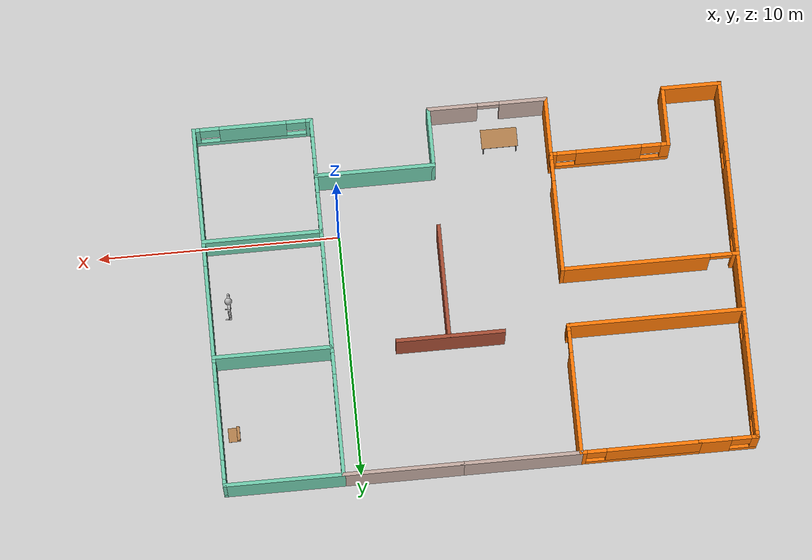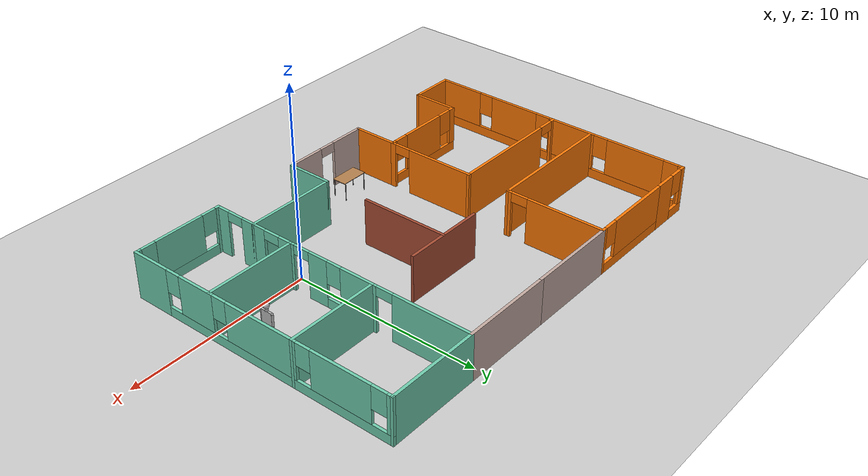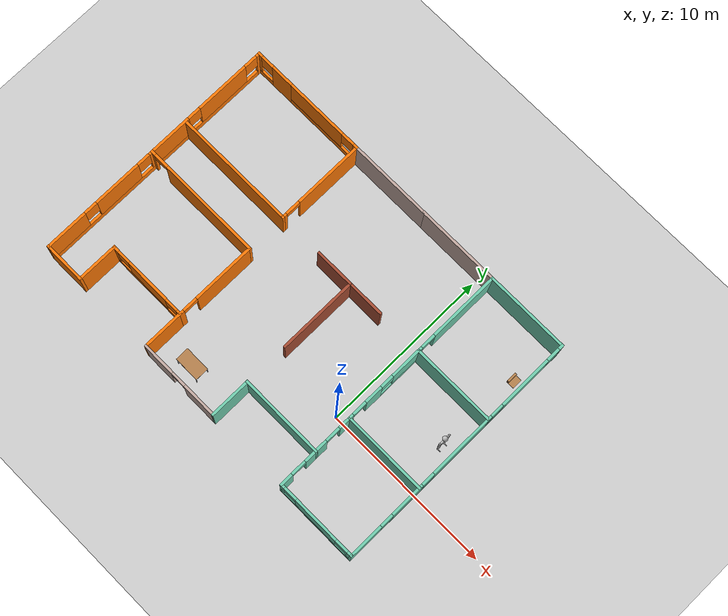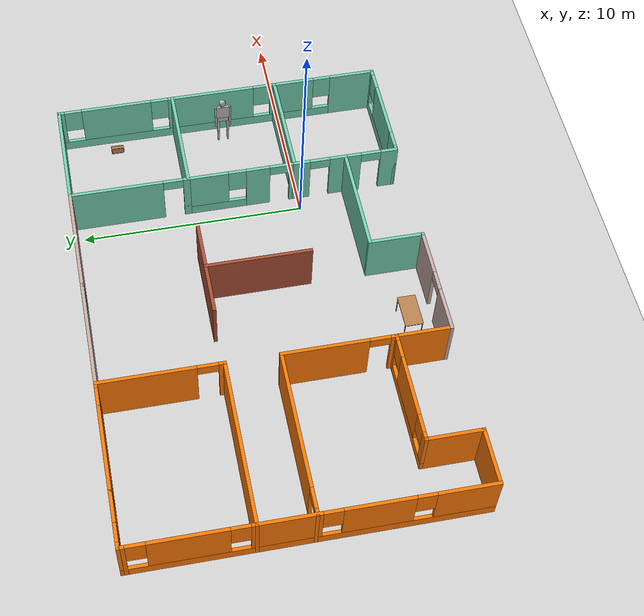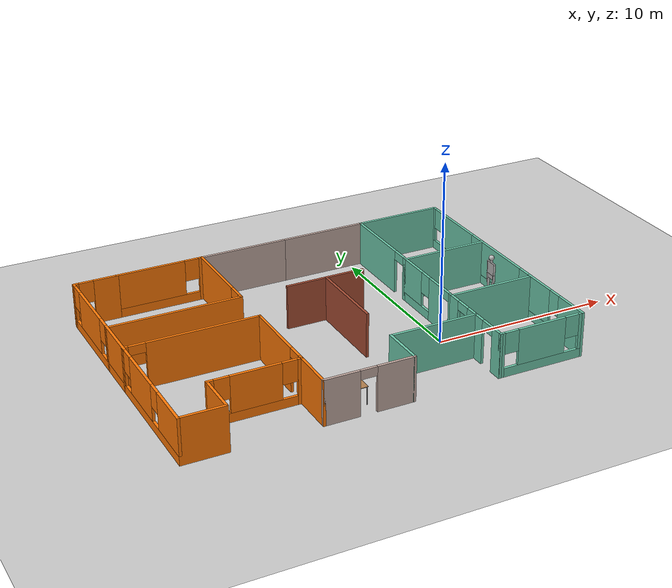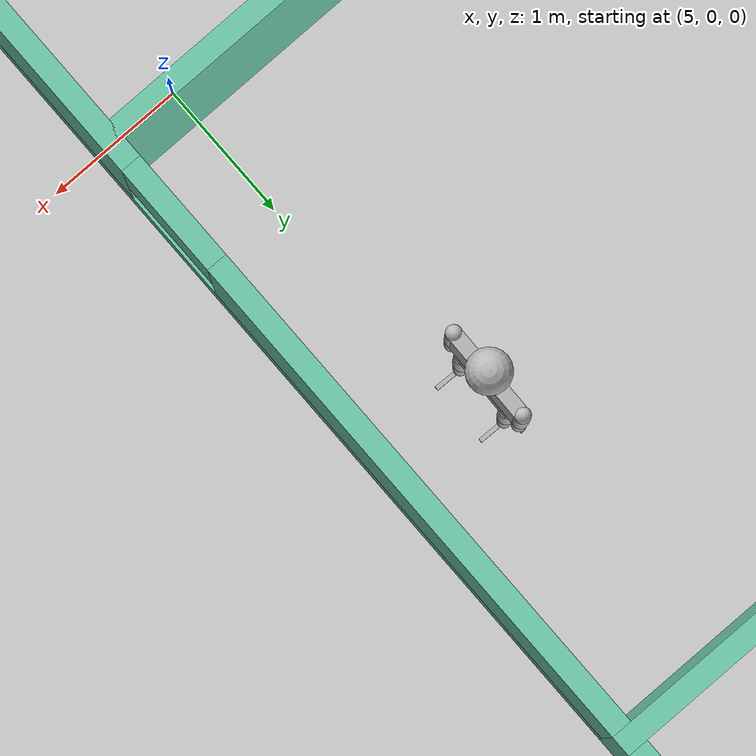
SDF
<sdf version="1.6">
 <world name="default">
  <plugin name="welcome_message" filename="libwelcome_message.so"/>
  <light name="sun" type="directional">
   <pose>0 0 10 0 -0 0</pose>
   <diffuse>0.8 0.8 0.8 1</diffuse>
   <specular>0.2 0.2 0.2 1</specular>
   <attenuation>
    <range>1000</range>
    <constant>0.9</constant>
    <linear>0.01</linear>
    <quadratic>0.001</quadratic>
   </attenuation>
   <direction>-0.5 0.1 -0.9</direction>
   <spot><inner_angle>0</inner_angle><outer_angle>0</outer_angle><falloff>0</falloff></spot>
  </light>
  <model name="ground_plane">
   <static>1</static>
   <link name="link">
    <collision name="collision">
     <geometry><plane><normal>0 0 1</normal><size>100 100</size></plane></geometry>
     <surface>
      <contact><collide_bitmask>65535</collide_bitmask></contact>
      <friction><ode><mu>100</mu><mu2>50</mu2></ode></friction>
     </surface>
    </collision>
    <visual name="visual">
     <cast_shadows>0</cast_shadows>
     <geometry><plane><normal>0 0 1</normal><size>100 100</size></plane></geometry>
     <material>
      <script><uri>file://media/materials/scripts/gazebo.material</uri><name>Gazebo/Grey</name></script>
     </material>
    </visual>
   </link>
  </model>
  <gravity>0 0 -9.8</gravity>
  <magnetic_field>6e-06 2.3e-05 -4.2e-05</magnetic_field>
  <atmosphere type="adiabatic"/>
  <physics name="default_physics" default="0" type="ode">
   <max_step_size>0.001</max_step_size>
   <real_time_factor>1</real_time_factor>
   <real_time_update_rate>1000</real_time_update_rate>
  </physics>
  <scene><ambient>0.4 0.4 0.4 1</ambient><background>0.7 0.7 0.7 1</background><shadows>1</shadows></scene>
  <spherical_coordinates>
   <surface_model>EARTH_WGS84</surface_model>
   <latitude_deg>0</latitude_deg>
   <longitude_deg>0</longitude_deg>
   <elevation>0</elevation>
   <heading_deg>0</heading_deg>
  </spherical_coordinates>
  <model name="World_1">
   <pose>-5.29578 2.9031 0 0 -0 0</pose>
   <link name="Wall_10">
    <pose>6.025 -3.9 0 0 -0 1.5708</pose>
    <visual name="Wall_10_Visual_0">
     <pose>-0.849577 0 1.25 0 -0 0</pose>
     <geometry><box><size>0.800846 0.15 2.5</size></box></geometry>
     <material>
      <script><uri>file://media/materials/scripts/gazebo.material</uri><name>Gazebo/Grey</name></script>
      <ambient>0.435294 0.796078 0.67451 1</ambient>
     </material>
     <meta><layer>0</layer></meta>
    </visual>
    <collision name="Wall_10_Collision_0">
     <geometry><box><size>0.800846 0.15 2.5</size></box></geometry>
     <pose>-0.849577 0 1.25 0 -0 0</pose>
    </collision>
    <visual name="Wall_10_Visual_1">
     <pose>0.850423 0 1.25 0 -0 0</pose>
     <geometry><box><size>0.799154 0.15 2.5</size></box></geometry>
     <material>
      <script><uri>file://media/materials/scripts/gazebo.material</uri><name>Gazebo/Grey</name></script>
      <ambient>0.435294 0.796078 0.67451 1</ambient>
     </material>
     <meta><layer>0</layer></meta>
    </visual>
    <collision name="Wall_10_Collision_1">
     <geometry><box><size>0.799154 0.15 2.5</size></box></geometry>
     <pose>0.850423 0 1.25 0 -0 0</pose>
    </collision>
    <visual name="Wall_10_Visual_2">
     <pose>0.000846 0 2.25 0 -0 0</pose>
     <geometry><box><size>0.9 0.15 0.5</size></box></geometry>
     <material>
      <script><uri>file://media/materials/scripts/gazebo.material</uri><name>Gazebo/Grey</name></script>
      <ambient>0.435294 0.796078 0.67451 1</ambient>
     </material>
     <meta><layer>0</layer></meta>
    </visual>
    <collision name="Wall_10_Collision_2">
     <geometry><box><size>0.9 0.15 0.5</size></box></geometry>
     <pose>0.000846 0 2.25 0 -0 0</pose>
    </collision>
   </link>
   <link name="Wall_11">
    <collision name="Wall_11_Collision">
     <geometry><box><size>5 0.15 2.5</size></box></geometry>
     <pose>0 0 1.25 0 -0 0</pose>
    </collision>
    <visual name="Wall_11_Visual">
     <pose>0 0 1.25 0 -0 0</pose>
     <geometry><box><size>5 0.15 2.5</size></box></geometry>
     <material>
      <script><uri>file://media/materials/scripts/gazebo.material</uri><name>Gazebo/Grey</name></script>
      <ambient>0.435294 0.796078 0.67451 1</ambient>
     </material>
     <meta><layer>0</layer></meta>
    </visual>
    <pose>8.45 -2.725 0 0 -0 0</pose>
   </link>
   <link name="Wall_13">
    <pose>6.025 -0.3 0 0 -0 1.5708</pose>
    <visual name="Wall_13_Visual_0">
     <pose>-2.34458 0 1.25 0 -0 0</pose>
     <geometry><box><size>0.310846 0.15 2.5</size></box></geometry>
     <material>
      <script><uri>file://media/materials/scripts/gazebo.material</uri><name>Gazebo/Grey</name></script>
      <ambient>0.435294 0.796078 0.67451 1</ambient>
     </material>
     <meta><layer>0</layer></meta>
    </visual>
    <collision name="Wall_13_Collision_0">
     <geometry><box><size>0.310846 0.15 2.5</size></box></geometry>
     <pose>-2.34458 0 1.25 0 -0 0</pose>
    </collision>
    <visual name="Wall_13_Visual_1">
     <pose>-0.744154 0 1.25 0 -0 0</pose>
     <geometry><box><size>1.09 0.15 2.5</size></box></geometry>
     <material>
      <script><uri>file://media/materials/scripts/gazebo.material</uri><name>Gazebo/Grey</name></script>
      <ambient>0.435294 0.796078 0.67451 1</ambient>
     </material>
     <meta><layer>0</layer></meta>
    </visual>
    <collision name="Wall_13_Collision_1">
     <geometry><box><size>1.09 0.15 2.5</size></box></geometry>
     <pose>-0.744154 0 1.25 0 -0 0</pose>
    </collision>
    <visual name="Wall_13_Visual_2">
     <pose>1.15042 0 0.25 0 -0 0</pose>
     <geometry><box><size>2.69915 0.15 0.5</size></box></geometry>
     <material>
      <script><uri>file://media/materials/scripts/gazebo.material</uri><name>Gazebo/Grey</name></script>
      <ambient>0.435294 0.796078 0.67451 1</ambient>
     </material>
     <meta><layer>0</layer></meta>
    </visual>
    <collision name="Wall_13_Collision_2">
     <geometry><box><size>2.69915 0.15 0.5</size></box></geometry>
     <pose>1.15042 0 0.25 0 -0 0</pose>
    </collision>
    <visual name="Wall_13_Visual_3">
     <pose>1.55042 0 1.5 0 -0 0</pose>
     <geometry><box><size>1.89915 0.15 2</size></box></geometry>
     <material>
      <script><uri>file://media/materials/scripts/gazebo.material</uri><name>Gazebo/Grey</name></script>
      <ambient>0.435294 0.796078 0.67451 1</ambient>
     </material>
     <meta><layer>0</layer></meta>
    </visual>
    <collision name="Wall_13_Collision_3">
     <geometry><box><size>1.89915 0.15 2</size></box></geometry>
     <pose>1.55042 0 1.5 0 -0 0</pose>
    </collision>
    <visual name="Wall_13_Visual_4">
     <pose>0.200846 0 1.9 0 -0 0</pose>
     <geometry><box><size>0.8 0.15 1.2</size></box></geometry>
     <material>
      <script><uri>file://media/materials/scripts/gazebo.material</uri><name>Gazebo/Grey</name></script>
      <ambient>0.435294 0.796078 0.67451 1</ambient>
     </material>
     <meta><layer>0</layer></meta>
    </visual>
    <collision name="Wall_13_Collision_4">
     <geometry><box><size>0.8 0.15 1.2</size></box></geometry>
     <pose>0.200846 0 1.9 0 -0 0</pose>
    </collision>
    <visual name="Wall_13_Visual_5">
     <pose>-1.73915 0 2.25 0 -0 0</pose>
     <geometry><box><size>0.9 0.15 0.5</size></box></geometry>
     <material>
      <script><uri>file://media/materials/scripts/gazebo.material</uri><name>Gazebo/Grey</name></script>
      <ambient>0.435294 0.796078 0.67451 1</ambient>
     </material>
     <meta><layer>0</layer></meta>
    </visual>
    <collision name="Wall_13_Collision_5">
     <geometry><box><size>0.9 0.15 0.5</size></box></geometry>
     <pose>-1.73915 0 2.25 0 -0 0</pose>
    </collision>
   </link>
   <link name="Wall_14">
    <collision name="Wall_14_Collision">
     <geometry><box><size>5 0.15 2.5</size></box></geometry>
     <pose>0 0 1.25 0 -0 0</pose>
    </collision>
    <visual name="Wall_14_Visual">
     <pose>0 0 1.25 0 -0 0</pose>
     <geometry><box><size>5 0.15 2.5</size></box></geometry>
     <material>
      <script><uri>file://media/materials/scripts/gazebo.material</uri><name>Gazebo/Grey</name></script>
      <ambient>0.435294 0.796078 0.67451 1</ambient>
     </material>
     <meta><layer>0</layer></meta>
    </visual>
    <pose>8.45 2.125 0 0 -0 0</pose>
   </link>
   <link name="Wall_16">
    <collision name="Wall_16_Collision">
     <geometry><box><size>5 0.15 2.5</size></box></geometry>
     <pose>0 0 1.25 0 -0 0</pose>
    </collision>
    <visual name="Wall_16_Visual">
     <pose>0 0 1.25 0 -0 0</pose>
     <geometry><box><size>5 0.15 2.5</size></box></geometry>
     <material>
      <script><uri>file://media/materials/scripts/gazebo.material</uri><name>Gazebo/Grey</name></script>
      <ambient>0.435294 0.796078 0.67451 1</ambient>
     </material>
     <meta><layer>0</layer></meta>
    </visual>
    <pose>8.45 7.425 0 0 -0 3.14159</pose>
   </link>
   <link name="Wall_17">
    <pose>6.025 4.775 0 0 0 -1.5708</pose>
    <visual name="Wall_17_Visual_0">
     <pose>-0.605423 0 1.25 0 -0 0</pose>
     <geometry><box><size>4.23915 0.15 2.5</size></box></geometry>
     <material>
      <script><uri>file://media/materials/scripts/gazebo.material</uri><name>Gazebo/Grey</name></script>
      <ambient>0.435294 0.796078 0.67451 1</ambient>
     </material>
     <meta><layer>0</layer></meta>
    </visual>
    <collision name="Wall_17_Collision_0">
     <geometry><box><size>4.23915 0.15 2.5</size></box></geometry>
     <pose>-0.605423 0 1.25 0 -0 0</pose>
    </collision>
    <visual name="Wall_17_Visual_1">
     <pose>2.56958 0 1.25 0 -0 0</pose>
     <geometry><box><size>0.310846 0.15 2.5</size></box></geometry>
     <material>
      <script><uri>file://media/materials/scripts/gazebo.material</uri><name>Gazebo/Grey</name></script>
      <ambient>0.435294 0.796078 0.67451 1</ambient>
     </material>
     <meta><layer>0</layer></meta>
    </visual>
    <collision name="Wall_17_Collision_1">
     <geometry><box><size>0.310846 0.15 2.5</size></box></geometry>
     <pose>2.56958 0 1.25 0 -0 0</pose>
    </collision>
    <visual name="Wall_17_Visual_2">
     <pose>1.96415 0 2.25 0 -0 0</pose>
     <geometry><box><size>0.9 0.15 0.5</size></box></geometry>
     <material>
      <script><uri>file://media/materials/scripts/gazebo.material</uri><name>Gazebo/Grey</name></script>
      <ambient>0.435294 0.796078 0.67451 1</ambient>
     </material>
     <meta><layer>0</layer></meta>
    </visual>
    <collision name="Wall_17_Collision_2">
     <geometry><box><size>0.9 0.15 0.5</size></box></geometry>
     <pose>1.96415 0 2.25 0 -0 0</pose>
    </collision>
   </link>
   <link name="Wall_19">
    <collision name="Wall_19_Collision">
     <geometry><box><size>2.5 0.15 2.5</size></box></geometry>
     <pose>0 0 1.25 0 -0 0</pose>
    </collision>
    <visual name="Wall_19_Visual">
     <pose>0 0 1.25 0 -0 0</pose>
     <geometry><box><size>2.5 0.15 2.5</size></box></geometry>
     <material>
      <script><uri>file://media/materials/scripts/gazebo.material</uri><name>Gazebo/Grey</name></script>
      <ambient>0.996078 0.47451 0.0196078 1</ambient>
     </material>
     <meta><layer>0</layer></meta>
    </visual>
    <pose>-3.675 -6.25 0 0 -0 1.5708</pose>
   </link>
   <link name="Wall_2">
    <pose>-1.25 -7.425 0 0 -0 0</pose>
    <visual name="Wall_2_Visual_0">
     <pose>-1.5042 0 1.25 0 -0 0</pose>
     <geometry><box><size>1.99161 0.15 2.5</size></box></geometry>
     <material>
      <script><uri>file://media/materials/scripts/gazebo.material</uri><name>Gazebo/Grey</name></script>
      <ambient>0.760784 0.662745 0.627451 1</ambient>
     </material>
     <meta><layer>0</layer></meta>
    </visual>
    <collision name="Wall_2_Collision_0">
     <geometry><box><size>1.99161 0.15 2.5</size></box></geometry>
     <pose>-1.5042 0 1.25 0 -0 0</pose>
    </collision>
    <visual name="Wall_2_Visual_1">
     <pose>1.4458 0 1.25 0 -0 0</pose>
     <geometry><box><size>2.10839 0.15 2.5</size></box></geometry>
     <material>
      <script><uri>file://media/materials/scripts/gazebo.material</uri><name>Gazebo/Grey</name></script>
      <ambient>0.760784 0.662745 0.627451 1</ambient>
     </material>
     <meta><layer>0</layer></meta>
    </visual>
    <collision name="Wall_2_Collision_1">
     <geometry><box><size>2.10839 0.15 2.5</size></box></geometry>
     <pose>1.4458 0 1.25 0 -0 0</pose>
    </collision>
    <visual name="Wall_2_Visual_2">
     <pose>-0.058393 0 2.25 0 -0 0</pose>
     <geometry><box><size>0.9 0.15 0.5</size></box></geometry>
     <material>
      <script><uri>file://media/materials/scripts/gazebo.material</uri><name>Gazebo/Grey</name></script>
      <ambient>0.760784 0.662745 0.627451 1</ambient>
     </material>
     <meta><layer>0</layer></meta>
    </visual>
    <collision name="Wall_2_Collision_2">
     <geometry><box><size>0.9 0.15 0.5</size></box></geometry>
     <pose>-0.058393 0 2.25 0 -0 0</pose>
    </collision>
   </link>
   <link name="Wall_21">
    <pose>-6.1 -5.075 0 0 -0 3.14159</pose>
    <visual name="Wall_21_Visual_0">
     <pose>-2.34529 0 1.25 0 -0 0</pose>
     <geometry><box><size>0.309417 0.15 2.5</size></box></geometry>
     <material>
      <script><uri>file://media/materials/scripts/gazebo.material</uri><name>Gazebo/Grey</name></script>
      <ambient>0.996078 0.47451 0.0196078 1</ambient>
     </material>
     <meta><layer>0</layer></meta>
    </visual>
    <collision name="Wall_21_Collision_0">
     <geometry><box><size>0.309417 0.15 2.5</size></box></geometry>
     <pose>-2.34529 0 1.25 0 -0 0</pose>
    </collision>
    <visual name="Wall_21_Visual_1">
     <pose>0.154709 0 0.25 0 -0 0</pose>
     <geometry><box><size>4.69058 0.15 0.5</size></box></geometry>
     <material>
      <script><uri>file://media/materials/scripts/gazebo.material</uri><name>Gazebo/Grey</name></script>
      <ambient>0.996078 0.47451 0.0196078 1</ambient>
     </material>
     <meta><layer>0</layer></meta>
    </visual>
    <collision name="Wall_21_Collision_1">
     <geometry><box><size>4.69058 0.15 0.5</size></box></geometry>
     <pose>0.154709 0 0.25 0 -0 0</pose>
    </collision>
    <visual name="Wall_21_Visual_2">
     <pose>-0.040702 0 1.5 0 -0 0</pose>
     <geometry><box><size>2.69976 0.15 2</size></box></geometry>
     <material>
      <script><uri>file://media/materials/scripts/gazebo.material</uri><name>Gazebo/Grey</name></script>
      <ambient>0.996078 0.47451 0.0196078 1</ambient>
     </material>
     <meta><layer>0</layer></meta>
    </visual>
    <collision name="Wall_21_Collision_2">
     <geometry><box><size>2.69976 0.15 2</size></box></geometry>
     <pose>-0.040702 0 1.5 0 -0 0</pose>
    </collision>
    <visual name="Wall_21_Visual_3">
     <pose>2.30459 0 1.5 0 -0 0</pose>
     <geometry><box><size>0.390821 0.15 2</size></box></geometry>
     <material>
      <script><uri>file://media/materials/scripts/gazebo.material</uri><name>Gazebo/Grey</name></script>
      <ambient>0.996078 0.47451 0.0196078 1</ambient>
     </material>
     <meta><layer>0</layer></meta>
    </visual>
    <collision name="Wall_21_Collision_3">
     <geometry><box><size>0.390821 0.15 2</size></box></geometry>
     <pose>2.30459 0 1.5 0 -0 0</pose>
    </collision>
    <visual name="Wall_21_Visual_4">
     <pose>-1.79058 0 1.9 0 -0 0</pose>
     <geometry><box><size>0.8 0.15 1.2</size></box></geometry>
     <material>
      <script><uri>file://media/materials/scripts/gazebo.material</uri><name>Gazebo/Grey</name></script>
      <ambient>0.996078 0.47451 0.0196078 1</ambient>
     </material>
     <meta><layer>0</layer></meta>
    </visual>
    <collision name="Wall_21_Collision_4">
     <geometry><box><size>0.8 0.15 1.2</size></box></geometry>
     <pose>-1.79058 0 1.9 0 -0 0</pose>
    </collision>
    <visual name="Wall_21_Visual_5">
     <pose>1.70918 0 1.9 0 -0 0</pose>
     <geometry><box><size>0.8 0.15 1.2</size></box></geometry>
     <material>
      <script><uri>file://media/materials/scripts/gazebo.material</uri><name>Gazebo/Grey</name></script>
      <ambient>0.996078 0.47451 0.0196078 1</ambient>
     </material>
     <meta><layer>0</layer></meta>
    </visual>
    <collision name="Wall_21_Collision_5">
     <geometry><box><size>0.8 0.15 1.2</size></box></geometry>
     <pose>1.70918 0 1.9 0 -0 0</pose>
    </collision>
   </link>
   <link name="Wall_3">
    <collision name="Wall_3_Collision">
     <geometry><box><size>2.5 0.15 2.5</size></box></geometry>
     <pose>0 0 1.25 0 -0 0</pose>
    </collision>
    <visual name="Wall_3_Visual">
     <pose>0 0 1.25 0 -0 0</pose>
     <geometry><box><size>2.5 0.15 2.5</size></box></geometry>
     <material>
      <script><uri>file://media/materials/scripts/gazebo.material</uri><name>Gazebo/Grey</name></script>
      <ambient>0.435294 0.796078 0.67451 1</ambient>
     </material>
     <meta><layer>0</layer></meta>
    </visual>
    <pose>1.175 -6.25 0 0 -0 1.5708</pose>
   </link>
   <link name="Wall_34">
    <collision name="Wall_34_Collision">
     <geometry><box><size>2.5 0.15 2.5</size></box></geometry>
     <pose>0 0 1.25 0 -0 0</pose>
    </collision>
    <visual name="Wall_34_Visual">
     <pose>0 0 1.25 0 -0 0</pose>
     <geometry><box><size>2.5 0.15 2.5</size></box></geometry>
     <material>
      <script><uri>file://media/materials/scripts/gazebo.material</uri><name>Gazebo/Grey</name></script>
      <ambient>0.996078 0.47451 0.0196078 1</ambient>
     </material>
     <meta><layer>0</layer></meta>
    </visual>
    <pose>-8.525 -6.25 0 0 0 -1.5708</pose>
   </link>
   <link name="Wall_38">
    <collision name="Wall_38_Collision">
     <geometry><box><size>5 0.15 2.5</size></box></geometry>
     <pose>0 0 1.25 0 -0 0</pose>
    </collision>
    <visual name="Wall_38_Visual">
     <pose>0 0 1.25 0 -0 0</pose>
     <geometry><box><size>5 0.15 2.5</size></box></geometry>
     <material>
      <script><uri>file://media/materials/scripts/gazebo.material</uri><name>Gazebo/Grey</name></script>
      <ambient>0.760784 0.662745 0.627451 1</ambient>
     </material>
     <meta><layer>0</layer></meta>
    </visual>
    <pose>3.6 7.425 0 0 -0 3.14159</pose>
   </link>
   <link name="Wall_39">
    <collision name="Wall_39_Collision">
     <geometry><box><size>5 0.15 2.5</size></box></geometry>
     <pose>0 0 1.25 0 -0 0</pose>
    </collision>
    <visual name="Wall_39_Visual">
     <pose>0 0 1.25 0 -0 0</pose>
     <geometry><box><size>5 0.15 2.5</size></box></geometry>
     <material>
      <script><uri>file://media/materials/scripts/gazebo.material</uri><name>Gazebo/Grey</name></script>
      <ambient>0.760784 0.662745 0.627451 1</ambient>
     </material>
     <meta><layer>0</layer></meta>
    </visual>
    <pose>-1.25 7.425 0 0 -0 3.14159</pose>
   </link>
   <link name="Wall_4">
    <collision name="Wall_4_Collision">
     <geometry><box><size>5 0.15 2.5</size></box></geometry>
     <pose>0 0 1.25 0 -0 0</pose>
    </collision>
    <visual name="Wall_4_Visual">
     <pose>0 0 1.25 0 -0 0</pose>
     <geometry><box><size>5 0.15 2.5</size></box></geometry>
     <material>
      <script><uri>file://media/materials/scripts/gazebo.material</uri><name>Gazebo/Grey</name></script>
      <ambient>0.435294 0.796078 0.67451 1</ambient>
     </material>
     <meta><layer>0</layer></meta>
    </visual>
    <pose>3.6 -5.075 0 0 -0 0</pose>
   </link>
   <link name="Wall_40">
    <pose>-6.1 7.425 0 0 -0 3.14159</pose>
    <visual name="Wall_40_Visual_0">
     <pose>-2.3458 0 1.25 0 -0 0</pose>
     <geometry><box><size>0.308393 0.15 2.5</size></box></geometry>
     <material>
      <script><uri>file://media/materials/scripts/gazebo.material</uri><name>Gazebo/Grey</name></script>
      <ambient>0.996078 0.47451 0.0196078 1</ambient>
     </material>
     <meta><layer>0</layer></meta>
    </visual>
    <collision name="Wall_40_Collision_0">
     <geometry><box><size>0.308393 0.15 2.5</size></box></geometry>
     <pose>-2.3458 0 1.25 0 -0 0</pose>
    </collision>
    <visual name="Wall_40_Visual_1">
     <pose>0.154197 0 0.25 0 -0 0</pose>
     <geometry><box><size>4.69161 0.15 0.5</size></box></geometry>
     <material>
      <script><uri>file://media/materials/scripts/gazebo.material</uri><name>Gazebo/Grey</name></script>
      <ambient>0.996078 0.47451 0.0196078 1</ambient>
     </material>
     <meta><layer>0</layer></meta>
    </visual>
    <collision name="Wall_40_Collision_1">
     <geometry><box><size>4.69161 0.15 0.5</size></box></geometry>
     <pose>0.154197 0 0.25 0 -0 0</pose>
    </collision>
    <visual name="Wall_40_Visual_2">
     <pose>0.554197 0 1.5 0 -0 0</pose>
     <geometry><box><size>3.89161 0.15 2</size></box></geometry>
     <material>
      <script><uri>file://media/materials/scripts/gazebo.material</uri><name>Gazebo/Grey</name></script>
      <ambient>0.996078 0.47451 0.0196078 1</ambient>
     </material>
     <meta><layer>0</layer></meta>
    </visual>
    <collision name="Wall_40_Collision_2">
     <geometry><box><size>3.89161 0.15 2</size></box></geometry>
     <pose>0.554197 0 1.5 0 -0 0</pose>
    </collision>
    <visual name="Wall_40_Visual_3">
     <pose>-1.79161 0 1.9 0 -0 0</pose>
     <geometry><box><size>0.8 0.15 1.2</size></box></geometry>
     <material>
      <script><uri>file://media/materials/scripts/gazebo.material</uri><name>Gazebo/Grey</name></script>
      <ambient>0.996078 0.47451 0.0196078 1</ambient>
     </material>
     <meta><layer>0</layer></meta>
    </visual>
    <collision name="Wall_40_Collision_3">
     <geometry><box><size>0.8 0.15 1.2</size></box></geometry>
     <pose>-1.79161 0 1.9 0 -0 0</pose>
    </collision>
   </link>
   <link name="Wall_43">
    <collision name="Wall_43_Collision">
     <geometry><box><size>2.5 0.15 2.5</size></box></geometry>
     <pose>0 0 1.25 0 -0 0</pose>
    </collision>
    <visual name="Wall_43_Visual">
     <pose>0 0 1.25 0 -0 0</pose>
     <geometry><box><size>2.5 0.15 2.5</size></box></geometry>
     <material>
      <script><uri>file://media/materials/scripts/gazebo.material</uri><name>Gazebo/Grey</name></script>
      <ambient>0.996078 0.47451 0.0196078 1</ambient>
     </material>
     <meta><layer>0</layer></meta>
    </visual>
    <pose>-9.7 -7.425 0 0 -0 3.14159</pose>
   </link>
   <link name="Wall_45">
    <pose>-9.7 7.425 0 0 -0 3.14159</pose>
    <visual name="Wall_45_Visual_0">
     <pose>-0.560804 0 1.25 0 -0 0</pose>
     <geometry><box><size>1.37839 0.15 2.5</size></box></geometry>
     <material>
      <script><uri>file://media/materials/scripts/gazebo.material</uri><name>Gazebo/Grey</name></script>
      <ambient>0.996078 0.47451 0.0196078 1</ambient>
     </material>
     <meta><layer>0</layer></meta>
    </visual>
    <collision name="Wall_45_Collision_0">
     <geometry><box><size>1.37839 0.15 2.5</size></box></geometry>
     <pose>-0.560804 0 1.25 0 -0 0</pose>
    </collision>
    <visual name="Wall_45_Visual_1">
     <pose>0.689196 0 0.25 0 -0 0</pose>
     <geometry><box><size>1.12161 0.15 0.5</size></box></geometry>
     <material>
      <script><uri>file://media/materials/scripts/gazebo.material</uri><name>Gazebo/Grey</name></script>
      <ambient>0.996078 0.47451 0.0196078 1</ambient>
     </material>
     <meta><layer>0</layer></meta>
    </visual>
    <collision name="Wall_45_Collision_1">
     <geometry><box><size>1.12161 0.15 0.5</size></box></geometry>
     <pose>0.689196 0 0.25 0 -0 0</pose>
    </collision>
    <visual name="Wall_45_Visual_2">
     <pose>1.0892 0 1.5 0 -0 0</pose>
     <geometry><box><size>0.321607 0.15 2</size></box></geometry>
     <material>
      <script><uri>file://media/materials/scripts/gazebo.material</uri><name>Gazebo/Grey</name></script>
      <ambient>0.996078 0.47451 0.0196078 1</ambient>
     </material>
     <meta><layer>0</layer></meta>
    </visual>
    <collision name="Wall_45_Collision_2">
     <geometry><box><size>0.321607 0.15 2</size></box></geometry>
     <pose>1.0892 0 1.5 0 -0 0</pose>
    </collision>
    <visual name="Wall_45_Visual_3">
     <pose>0.528393 0 1.9 0 -0 0</pose>
     <geometry><box><size>0.8 0.15 1.2</size></box></geometry>
     <material>
      <script><uri>file://media/materials/scripts/gazebo.material</uri><name>Gazebo/Grey</name></script>
      <ambient>0.996078 0.47451 0.0196078 1</ambient>
     </material>
     <meta><layer>0</layer></meta>
    </visual>
    <collision name="Wall_45_Collision_3">
     <geometry><box><size>0.8 0.15 1.2</size></box></geometry>
     <pose>0.528393 0 1.9 0 -0 0</pose>
    </collision>
   </link>
   <link name="Wall_46">
    <pose>-10.875 0 0 0 0 -1.5708</pose>
    <visual name="Wall_46_Visual_0">
     <pose>-7.34042 0 1.25 0 -0 0</pose>
     <geometry><box><size>0.319154 0.15 2.5</size></box></geometry>
     <material>
      <script><uri>file://media/materials/scripts/gazebo.material</uri><name>Gazebo/Grey</name></script>
      <ambient>0.996078 0.47451 0.0196078 1</ambient>
     </material>
     <meta><layer>0</layer></meta>
    </visual>
    <collision name="Wall_46_Collision_0">
     <geometry><box><size>0.319154 0.15 2.5</size></box></geometry>
     <pose>-7.34042 0 1.25 0 -0 0</pose>
    </collision>
    <visual name="Wall_46_Visual_1">
     <pose>0.159577 0 0.25 0 -0 0</pose>
     <geometry><box><size>14.6808 0.15 0.5</size></box></geometry>
     <material>
      <script><uri>file://media/materials/scripts/gazebo.material</uri><name>Gazebo/Grey</name></script>
      <ambient>0.996078 0.47451 0.0196078 1</ambient>
     </material>
     <meta><layer>0</layer></meta>
    </visual>
    <collision name="Wall_46_Collision_1">
     <geometry><box><size>14.6808 0.15 0.5</size></box></geometry>
     <pose>0.159577 0 0.25 0 -0 0</pose>
    </collision>
    <visual name="Wall_46_Visual_2">
     <pose>-4.75585 0 1.5 0 -0 0</pose>
     <geometry><box><size>3.25 0.15 2</size></box></geometry>
     <material>
      <script><uri>file://media/materials/scripts/gazebo.material</uri><name>Gazebo/Grey</name></script>
      <ambient>0.996078 0.47451 0.0196078 1</ambient>
     </material>
     <meta><layer>0</layer></meta>
    </visual>
    <collision name="Wall_46_Collision_2">
     <geometry><box><size>3.25 0.15 2</size></box></geometry>
     <pose>-4.75585 0 1.5 0 -0 0</pose>
    </collision>
    <visual name="Wall_46_Visual_3">
     <pose>-0.940846 0 1.5 0 -0 0</pose>
     <geometry><box><size>2.78 0.15 2</size></box></geometry>
     <material>
      <script><uri>file://media/materials/scripts/gazebo.material</uri><name>Gazebo/Grey</name></script>
      <ambient>0.996078 0.47451 0.0196078 1</ambient>
     </material>
     <meta><layer>0</layer></meta>
    </visual>
    <collision name="Wall_46_Collision_3">
     <geometry><box><size>2.78 0.15 2</size></box></geometry>
     <pose>-0.940846 0 1.5 0 -0 0</pose>
    </collision>
    <visual name="Wall_46_Visual_4">
     <pose>2.68915 0 1.5 0 -0 0</pose>
     <geometry><box><size>2.88 0.15 2</size></box></geometry>
     <material>
      <script><uri>file://media/materials/scripts/gazebo.material</uri><name>Gazebo/Grey</name></script>
      <ambient>0.996078 0.47451 0.0196078 1</ambient>
     </material>
     <meta><layer>0</layer></meta>
    </visual>
    <collision name="Wall_46_Collision_4">
     <geometry><box><size>2.88 0.15 2</size></box></geometry>
     <pose>2.68915 0 1.5 0 -0 0</pose>
    </collision>
    <visual name="Wall_46_Visual_5">
     <pose>6.21458 0 1.5 0 -0 0</pose>
     <geometry><box><size>2.57085 0.15 2</size></box></geometry>
     <material>
      <script><uri>file://media/materials/scripts/gazebo.material</uri><name>Gazebo/Grey</name></script>
      <ambient>0.996078 0.47451 0.0196078 1</ambient>
     </material>
     <meta><layer>0</layer></meta>
    </visual>
    <collision name="Wall_46_Collision_5">
     <geometry><box><size>2.57085 0.15 2</size></box></geometry>
     <pose>6.21458 0 1.5 0 -0 0</pose>
    </collision>
    <visual name="Wall_46_Visual_6">
     <pose>-6.78085 0 1.9 0 -0 0</pose>
     <geometry><box><size>0.8 0.15 1.2</size></box></geometry>
     <material>
      <script><uri>file://media/materials/scripts/gazebo.material</uri><name>Gazebo/Grey</name></script>
      <ambient>0.996078 0.47451 0.0196078 1</ambient>
     </material>
     <meta><layer>0</layer></meta>
    </visual>
    <collision name="Wall_46_Collision_6">
     <geometry><box><size>0.8 0.15 1.2</size></box></geometry>
     <pose>-6.78085 0 1.9 0 -0 0</pose>
    </collision>
    <visual name="Wall_46_Visual_7">
     <pose>-2.73085 0 1.9 0 -0 0</pose>
     <geometry><box><size>0.8 0.15 1.2</size></box></geometry>
     <material>
      <script><uri>file://media/materials/scripts/gazebo.material</uri><name>Gazebo/Grey</name></script>
      <ambient>0.996078 0.47451 0.0196078 1</ambient>
     </material>
     <meta><layer>0</layer></meta>
    </visual>
    <collision name="Wall_46_Collision_7">
     <geometry><box><size>0.8 0.15 1.2</size></box></geometry>
     <pose>-2.73085 0 1.9 0 -0 0</pose>
    </collision>
    <visual name="Wall_46_Visual_8">
     <pose>0.849154 0 1.9 0 -0 0</pose>
     <geometry><box><size>0.8 0.15 1.2</size></box></geometry>
     <material>
      <script><uri>file://media/materials/scripts/gazebo.material</uri><name>Gazebo/Grey</name></script>
      <ambient>0.996078 0.47451 0.0196078 1</ambient>
     </material>
     <meta><layer>0</layer></meta>
    </visual>
    <collision name="Wall_46_Collision_8">
     <geometry><box><size>0.8 0.15 1.2</size></box></geometry>
     <pose>0.849154 0 1.9 0 -0 0</pose>
    </collision>
    <visual name="Wall_46_Visual_9">
     <pose>4.52915 0 1.9 0 -0 0</pose>
     <geometry><box><size>0.8 0.15 1.2</size></box></geometry>
     <material>
      <script><uri>file://media/materials/scripts/gazebo.material</uri><name>Gazebo/Grey</name></script>
      <ambient>0.996078 0.47451 0.0196078 1</ambient>
     </material>
     <meta><layer>0</layer></meta>
    </visual>
    <collision name="Wall_46_Collision_9">
     <geometry><box><size>0.8 0.15 1.2</size></box></geometry>
     <pose>4.52915 0 1.9 0 -0 0</pose>
    </collision>
   </link>
   <link name="Wall_48">
    <pose>-3.675 -2.65 0 0 -0 1.5708</pose>
    <visual name="Wall_48_Visual_0">
     <pose>-2.34458 0 1.25 0 -0 0</pose>
     <geometry><box><size>0.310846 0.15 2.5</size></box></geometry>
     <material>
      <script><uri>file://media/materials/scripts/gazebo.material</uri><name>Gazebo/Grey</name></script>
      <ambient>0.996078 0.47451 0.0196078 1</ambient>
     </material>
     <meta><layer>0</layer></meta>
    </visual>
    <collision name="Wall_48_Collision_0">
     <geometry><box><size>0.310846 0.15 2.5</size></box></geometry>
     <pose>-2.34458 0 1.25 0 -0 0</pose>
    </collision>
    <visual name="Wall_48_Visual_1">
     <pose>0.605423 0 1.25 0 -0 0</pose>
     <geometry><box><size>3.78915 0.15 2.5</size></box></geometry>
     <material>
      <script><uri>file://media/materials/scripts/gazebo.material</uri><name>Gazebo/Grey</name></script>
      <ambient>0.996078 0.47451 0.0196078 1</ambient>
     </material>
     <meta><layer>0</layer></meta>
    </visual>
    <collision name="Wall_48_Collision_1">
     <geometry><box><size>3.78915 0.15 2.5</size></box></geometry>
     <pose>0.605423 0 1.25 0 -0 0</pose>
    </collision>
    <visual name="Wall_48_Visual_2">
     <pose>-1.73915 0 2.25 0 -0 0</pose>
     <geometry><box><size>0.9 0.15 0.5</size></box></geometry>
     <material>
      <script><uri>file://media/materials/scripts/gazebo.material</uri><name>Gazebo/Grey</name></script>
      <ambient>0.996078 0.47451 0.0196078 1</ambient>
     </material>
     <meta><layer>0</layer></meta>
    </visual>
    <collision name="Wall_48_Collision_2">
     <geometry><box><size>0.9 0.15 0.5</size></box></geometry>
     <pose>-1.73915 0 2.25 0 -0 0</pose>
    </collision>
   </link>
   <link name="Wall_5">
    <pose>6.025 -6.25 0 0 0 -1.5708</pose>
    <visual name="Wall_5_Visual_0">
     <pose>-0.845423 0 1.25 0 -0 0</pose>
     <geometry><box><size>0.809154 0.15 2.5</size></box></geometry>
     <material>
      <script><uri>file://media/materials/scripts/gazebo.material</uri><name>Gazebo/Grey</name></script>
      <ambient>0.435294 0.796078 0.67451 1</ambient>
     </material>
     <meta><layer>0</layer></meta>
    </visual>
    <collision name="Wall_5_Collision_0">
     <geometry><box><size>0.809154 0.15 2.5</size></box></geometry>
     <pose>-0.845423 0 1.25 0 -0 0</pose>
    </collision>
    <visual name="Wall_5_Visual_1">
     <pose>0.854577 0 1.25 0 -0 0</pose>
     <geometry><box><size>0.790846 0.15 2.5</size></box></geometry>
     <material>
      <script><uri>file://media/materials/scripts/gazebo.material</uri><name>Gazebo/Grey</name></script>
      <ambient>0.435294 0.796078 0.67451 1</ambient>
     </material>
     <meta><layer>0</layer></meta>
    </visual>
    <collision name="Wall_5_Collision_1">
     <geometry><box><size>0.790846 0.15 2.5</size></box></geometry>
     <pose>0.854577 0 1.25 0 -0 0</pose>
    </collision>
    <visual name="Wall_5_Visual_2">
     <pose>0.009154 0 2.25 0 -0 0</pose>
     <geometry><box><size>0.9 0.15 0.5</size></box></geometry>
     <material>
      <script><uri>file://media/materials/scripts/gazebo.material</uri><name>Gazebo/Grey</name></script>
      <ambient>0.435294 0.796078 0.67451 1</ambient>
     </material>
     <meta><layer>0</layer></meta>
    </visual>
    <collision name="Wall_5_Collision_2">
     <geometry><box><size>0.9 0.15 0.5</size></box></geometry>
     <pose>0.009154 0 2.25 0 -0 0</pose>
    </collision>
   </link>
   <link name="Wall_50">
    <pose>-7.275 -0.225 0 0 -0 3.14159</pose>
    <visual name="Wall_50_Visual_0">
     <pose>-0.605803 0 1.25 0 -0 0</pose>
     <geometry><box><size>6.13839 0.15 2.5</size></box></geometry>
     <material>
      <script><uri>file://media/materials/scripts/gazebo.material</uri><name>Gazebo/Grey</name></script>
      <ambient>0.996078 0.47451 0.0196078 1</ambient>
     </material>
     <meta><layer>0</layer></meta>
    </visual>
    <collision name="Wall_50_Collision_0">
     <geometry><box><size>6.13839 0.15 2.5</size></box></geometry>
     <pose>-0.605803 0 1.25 0 -0 0</pose>
    </collision>
    <visual name="Wall_50_Visual_1">
     <pose>3.5192 0 1.25 0 -0 0</pose>
     <geometry><box><size>0.311607 0.15 2.5</size></box></geometry>
     <material>
      <script><uri>file://media/materials/scripts/gazebo.material</uri><name>Gazebo/Grey</name></script>
      <ambient>0.996078 0.47451 0.0196078 1</ambient>
     </material>
     <meta><layer>0</layer></meta>
    </visual>
    <collision name="Wall_50_Collision_1">
     <geometry><box><size>0.311607 0.15 2.5</size></box></geometry>
     <pose>3.5192 0 1.25 0 -0 0</pose>
    </collision>
    <visual name="Wall_50_Visual_2">
     <pose>2.91339 0 2.25 0 -0 0</pose>
     <geometry><box><size>0.9 0.15 0.5</size></box></geometry>
     <material>
      <script><uri>file://media/materials/scripts/gazebo.material</uri><name>Gazebo/Grey</name></script>
      <ambient>0.996078 0.47451 0.0196078 1</ambient>
     </material>
     <meta><layer>0</layer></meta>
    </visual>
    <collision name="Wall_50_Collision_2">
     <geometry><box><size>0.9 0.15 0.5</size></box></geometry>
     <pose>2.91339 0 2.25 0 -0 0</pose>
    </collision>
   </link>
   <link name="Wall_53">
    <pose>-3.675 4.775 0 0 0 -1.5708</pose>
    <visual name="Wall_53_Visual_0">
     <pose>-0.610423 0 1.25 0 -0 0</pose>
     <geometry><box><size>4.22915 0.15 2.5</size></box></geometry>
     <material>
      <script><uri>file://media/materials/scripts/gazebo.material</uri><name>Gazebo/Grey</name></script>
      <ambient>0.996078 0.47451 0.0196078 1</ambient>
     </material>
     <meta><layer>0</layer></meta>
    </visual>
    <collision name="Wall_53_Collision_0">
     <geometry><box><size>4.22915 0.15 2.5</size></box></geometry>
     <pose>-0.610423 0 1.25 0 -0 0</pose>
    </collision>
    <visual name="Wall_53_Visual_1">
     <pose>2.56458 0 1.25 0 -0 0</pose>
     <geometry><box><size>0.320846 0.15 2.5</size></box></geometry>
     <material>
      <script><uri>file://media/materials/scripts/gazebo.material</uri><name>Gazebo/Grey</name></script>
      <ambient>0.996078 0.47451 0.0196078 1</ambient>
     </material>
     <meta><layer>0</layer></meta>
    </visual>
    <collision name="Wall_53_Collision_1">
     <geometry><box><size>0.320846 0.15 2.5</size></box></geometry>
     <pose>2.56458 0 1.25 0 -0 0</pose>
    </collision>
    <visual name="Wall_53_Visual_2">
     <pose>1.95415 0 2.25 0 -0 0</pose>
     <geometry><box><size>0.9 0.15 0.5</size></box></geometry>
     <material>
      <script><uri>file://media/materials/scripts/gazebo.material</uri><name>Gazebo/Grey</name></script>
      <ambient>0.996078 0.47451 0.0196078 1</ambient>
     </material>
     <meta><layer>0</layer></meta>
    </visual>
    <collision name="Wall_53_Collision_2">
     <geometry><box><size>0.9 0.15 0.5</size></box></geometry>
     <pose>1.95415 0 2.25 0 -0 0</pose>
    </collision>
   </link>
   <link name="Wall_55">
    <collision name="Wall_55_Collision">
     <geometry><box><size>7.35 0.15 2.5</size></box></geometry>
     <pose>0 0 1.25 0 -0 0</pose>
    </collision>
    <visual name="Wall_55_Visual">
     <pose>0 0 1.25 0 -0 0</pose>
     <geometry><box><size>7.35 0.15 2.5</size></box></geometry>
     <material>
      <script><uri>file://media/materials/scripts/gazebo.material</uri><name>Gazebo/Grey</name></script>
      <ambient>0.996078 0.47451 0.0196078 1</ambient>
     </material>
     <meta><layer>0</layer></meta>
    </visual>
    <pose>-7.275 2.125 0 0 -0 3.14159</pose>
   </link>
   <link name="Wall_57">
    <collision name="Wall_57_Collision">
     <geometry><box><size>4.5 0.15 2.5</size></box></geometry>
     <pose>0 0 1.25 0 -0 0</pose>
    </collision>
    <visual name="Wall_57_Visual">
     <pose>0 0 1.25 0 -0 0</pose>
     <geometry><box><size>4.5 0.15 2.5</size></box></geometry>
     <material>
      <script><uri>file://media/materials/scripts/gazebo.material</uri><name>Gazebo/Bricks</name></script>
      <ambient>1 1 1 1</ambient>
     </material>
     <meta><layer>0</layer></meta>
    </visual>
    <pose>1.15173 2.11728 0 0 -0 0</pose>
   </link>
   <link name="Wall_59">
    <collision name="Wall_59_Collision">
     <geometry><box><size>4.75 0.15 2.5</size></box></geometry>
     <pose>0 0 1.25 0 -0 0</pose>
    </collision>
    <visual name="Wall_59_Visual">
     <pose>0 0 1.25 0 -0 0</pose>
     <geometry><box><size>4.75 0.15 2.5</size></box></geometry>
     <material>
      <script><uri>file://media/materials/scripts/gazebo.material</uri><name>Gazebo/Bricks</name></script>
      <ambient>1 1 1 1</ambient>
     </material>
     <meta><layer>0</layer></meta>
    </visual>
    <pose>1.20673 -0.182724 0 0 0 -1.5708</pose>
   </link>
   <link name="Wall_6">
    <pose>8.45 -7.425 0 0 -0 0</pose>
    <visual name="Wall_6_Visual_0">
     <pose>-2.3492 0 1.25 0 -0 0</pose>
     <geometry><box><size>0.301607 0.15 2.5</size></box></geometry>
     <material>
      <script><uri>file://media/materials/scripts/gazebo.material</uri><name>Gazebo/Grey</name></script>
      <ambient>0.435294 0.796078 0.67451 1</ambient>
     </material>
     <meta><layer>0</layer></meta>
    </visual>
    <collision name="Wall_6_Collision_0">
     <geometry><box><size>0.301607 0.15 2.5</size></box></geometry>
     <pose>-2.3492 0 1.25 0 -0 0</pose>
    </collision>
    <visual name="Wall_6_Visual_1">
     <pose>0.150803 0 0.25 0 -0 0</pose>
     <geometry><box><size>4.69839 0.15 0.5</size></box></geometry>
     <material>
      <script><uri>file://media/materials/scripts/gazebo.material</uri><name>Gazebo/Grey</name></script>
      <ambient>0.435294 0.796078 0.67451 1</ambient>
     </material>
     <meta><layer>0</layer></meta>
    </visual>
    <collision name="Wall_6_Collision_1">
     <geometry><box><size>4.69839 0.15 0.5</size></box></geometry>
     <pose>0.150803 0 0.25 0 -0 0</pose>
    </collision>
    <visual name="Wall_6_Visual_2">
     <pose>-0.013393 0 1.5 0 -0 0</pose>
     <geometry><box><size>2.77 0.15 2</size></box></geometry>
     <material>
      <script><uri>file://media/materials/scripts/gazebo.material</uri><name>Gazebo/Grey</name></script>
      <ambient>0.435294 0.796078 0.67451 1</ambient>
     </material>
     <meta><layer>0</layer></meta>
    </visual>
    <collision name="Wall_6_Collision_2">
     <geometry><box><size>2.77 0.15 2</size></box></geometry>
     <pose>-0.013393 0 1.5 0 -0 0</pose>
    </collision>
    <visual name="Wall_6_Visual_3">
     <pose>2.3358 0 1.5 0 -0 0</pose>
     <geometry><box><size>0.328393 0.15 2</size></box></geometry>
     <material>
      <script><uri>file://media/materials/scripts/gazebo.material</uri><name>Gazebo/Grey</name></script>
      <ambient>0.435294 0.796078 0.67451 1</ambient>
     </material>
     <meta><layer>0</layer></meta>
    </visual>
    <collision name="Wall_6_Collision_3">
     <geometry><box><size>0.328393 0.15 2</size></box></geometry>
     <pose>2.3358 0 1.5 0 -0 0</pose>
    </collision>
    <visual name="Wall_6_Visual_4">
     <pose>-1.79839 0 1.9 0 -0 0</pose>
     <geometry><box><size>0.8 0.15 1.2</size></box></geometry>
     <material>
      <script><uri>file://media/materials/scripts/gazebo.material</uri><name>Gazebo/Grey</name></script>
      <ambient>0.435294 0.796078 0.67451 1</ambient>
     </material>
     <meta><layer>0</layer></meta>
    </visual>
    <collision name="Wall_6_Collision_4">
     <geometry><box><size>0.8 0.15 1.2</size></box></geometry>
     <pose>-1.79839 0 1.9 0 -0 0</pose>
    </collision>
    <visual name="Wall_6_Visual_5">
     <pose>1.77161 0 1.9 0 -0 0</pose>
     <geometry><box><size>0.8 0.15 1.2</size></box></geometry>
     <material>
      <script><uri>file://media/materials/scripts/gazebo.material</uri><name>Gazebo/Grey</name></script>
      <ambient>0.435294 0.796078 0.67451 1</ambient>
     </material>
     <meta><layer>0</layer></meta>
    </visual>
    <collision name="Wall_6_Collision_5">
     <geometry><box><size>0.8 0.15 1.2</size></box></geometry>
     <pose>1.77161 0 1.9 0 -0 0</pose>
    </collision>
   </link>
   <link name="Wall_8">
    <pose>10.875 0 0 0 -0 1.5708</pose>
    <visual name="Wall_8_Visual_0">
     <pose>-6.44458 0 1.25 0 -0 0</pose>
     <geometry><box><size>2.11085 0.15 2.5</size></box></geometry>
     <material>
      <script><uri>file://media/materials/scripts/gazebo.material</uri><name>Gazebo/Grey</name></script>
      <ambient>0.435294 0.796078 0.67451 1</ambient>
     </material>
     <meta><layer>0</layer></meta>
    </visual>
    <collision name="Wall_8_Collision_0">
     <geometry><box><size>2.11085 0.15 2.5</size></box></geometry>
     <pose>-6.44458 0 1.25 0 -0 0</pose>
    </collision>
    <visual name="Wall_8_Visual_1">
     <pose>1.05542 0 0.25 0 -0 0</pose>
     <geometry><box><size>12.8892 0.15 0.5</size></box></geometry>
     <material>
      <script><uri>file://media/materials/scripts/gazebo.material</uri><name>Gazebo/Grey</name></script>
      <ambient>0.435294 0.796078 0.67451 1</ambient>
     </material>
     <meta><layer>0</layer></meta>
    </visual>
    <collision name="Wall_8_Collision_1">
     <geometry><box><size>12.8892 0.15 0.5</size></box></geometry>
     <pose>1.05542 0 0.25 0 -0 0</pose>
    </collision>
    <visual name="Wall_8_Visual_2">
     <pose>-3.54915 0 1.5 0 -0 0</pose>
     <geometry><box><size>2.08 0.15 2</size></box></geometry>
     <material>
      <script><uri>file://media/materials/scripts/gazebo.material</uri><name>Gazebo/Grey</name></script>
      <ambient>0.435294 0.796078 0.67451 1</ambient>
     </material>
     <meta><layer>0</layer></meta>
    </visual>
    <collision name="Wall_8_Collision_2">
     <geometry><box><size>2.08 0.15 2</size></box></geometry>
     <pose>-3.54915 0 1.5 0 -0 0</pose>
    </collision>
    <visual name="Wall_8_Visual_3">
     <pose>0.315846 0 1.5 0 -0 0</pose>
     <geometry><box><size>4.05 0.15 2</size></box></geometry>
     <material>
      <script><uri>file://media/materials/scripts/gazebo.material</uri><name>Gazebo/Grey</name></script>
      <ambient>0.435294 0.796078 0.67451 1</ambient>
     </material>
     <meta><layer>0</layer></meta>
    </visual>
    <collision name="Wall_8_Collision_3">
     <geometry><box><size>4.05 0.15 2</size></box></geometry>
     <pose>0.315846 0 1.5 0 -0 0</pose>
    </collision>
    <visual name="Wall_8_Visual_4">
     <pose>4.76085 0 1.5 0 -0 0</pose>
     <geometry><box><size>3.24 0.15 2</size></box></geometry>
     <material>
      <script><uri>file://media/materials/scripts/gazebo.material</uri><name>Gazebo/Grey</name></script>
      <ambient>0.435294 0.796078 0.67451 1</ambient>
     </material>
     <meta><layer>0</layer></meta>
    </visual>
    <collision name="Wall_8_Collision_4">
     <geometry><box><size>3.24 0.15 2</size></box></geometry>
     <pose>4.76085 0 1.5 0 -0 0</pose>
    </collision>
    <visual name="Wall_8_Visual_5">
     <pose>7.34042 0 1.5 0 -0 0</pose>
     <geometry><box><size>0.319154 0.15 2</size></box></geometry>
     <material>
      <script><uri>file://media/materials/scripts/gazebo.material</uri><name>Gazebo/Grey</name></script>
      <ambient>0.435294 0.796078 0.67451 1</ambient>
     </material>
     <meta><layer>0</layer></meta>
    </visual>
    <collision name="Wall_8_Collision_5">
     <geometry><box><size>0.319154 0.15 2</size></box></geometry>
     <pose>7.34042 0 1.5 0 -0 0</pose>
    </collision>
    <visual name="Wall_8_Visual_6">
     <pose>-4.98915 0 1.9 0 -0 0</pose>
     <geometry><box><size>0.8 0.15 1.2</size></box></geometry>
     <material>
      <script><uri>file://media/materials/scripts/gazebo.material</uri><name>Gazebo/Grey</name></script>
      <ambient>0.435294 0.796078 0.67451 1</ambient>
     </material>
     <meta><layer>0</layer></meta>
    </visual>
    <collision name="Wall_8_Collision_6">
     <geometry><box><size>0.8 0.15 1.2</size></box></geometry>
     <pose>-4.98915 0 1.9 0 -0 0</pose>
    </collision>
    <visual name="Wall_8_Visual_7">
     <pose>-2.10915 0 1.9 0 -0 0</pose>
     <geometry><box><size>0.8 0.15 1.2</size></box></geometry>
     <material>
      <script><uri>file://media/materials/scripts/gazebo.material</uri><name>Gazebo/Grey</name></script>
      <ambient>0.435294 0.796078 0.67451 1</ambient>
     </material>
     <meta><layer>0</layer></meta>
    </visual>
    <collision name="Wall_8_Collision_7">
     <geometry><box><size>0.8 0.15 1.2</size></box></geometry>
     <pose>-2.10915 0 1.9 0 -0 0</pose>
    </collision>
    <visual name="Wall_8_Visual_8">
     <pose>2.74085 0 1.9 0 -0 0</pose>
     <geometry><box><size>0.8 0.15 1.2</size></box></geometry>
     <material>
      <script><uri>file://media/materials/scripts/gazebo.material</uri><name>Gazebo/Grey</name></script>
      <ambient>0.435294 0.796078 0.67451 1</ambient>
     </material>
     <meta><layer>0</layer></meta>
    </visual>
    <collision name="Wall_8_Collision_8">
     <geometry><box><size>0.8 0.15 1.2</size></box></geometry>
     <pose>2.74085 0 1.9 0 -0 0</pose>
    </collision>
    <visual name="Wall_8_Visual_9">
     <pose>6.78085 0 1.9 0 -0 0</pose>
     <geometry><box><size>0.8 0.15 1.2</size></box></geometry>
     <material>
      <script><uri>file://media/materials/scripts/gazebo.material</uri><name>Gazebo/Grey</name></script>
      <ambient>0.435294 0.796078 0.67451 1</ambient>
     </material>
     <meta><layer>0</layer></meta>
    </visual>
    <collision name="Wall_8_Collision_9">
     <geometry><box><size>0.8 0.15 1.2</size></box></geometry>
     <pose>6.78085 0 1.9 0 -0 0</pose>
    </collision>
   </link>
   <static>1</static>
  </model>
  <model name="ragdoll">
   <pose>4.76841 2.78673 1.39999 -2e-06 -0.000973 -0.017222</pose>
   <link name="hip">
    <inertial>
     <inertia><ixx>0.1</ixx><ixy>0</ixy><ixz>0</ixz><iyy>0.1</iyy><iyz>0</iyz><izz>0.1</izz></inertia>
     <mass>10</mass>
    </inertial>
    <collision name="hip_geom">
     <pose>0 0 0.125 0 -0 0</pose>
     <geometry><box><size>0.1 0.5 0.25</size></box></geometry>
     <surface>
      <friction><ode><mu>-1</mu><mu2>-1</mu2><fdir1>0 0 0</fdir1><slip1>0</slip1><slip2>0</slip2></ode></friction>
      <bounce><restitution_coefficient>0</restitution_coefficient><threshold>100000</threshold></bounce>
      <contact>
       <ode>
        <soft_cfm>0</soft_cfm>
        <soft_erp>0.2</soft_erp>
        <kp>1e+12</kp>
        <kd>1</kd>
        <max_vel>0</max_vel>
        <min_depth>0.001</min_depth>
       </ode>
      </contact>
     </surface>
    </collision>
    <visual name="hip_geom_visual">
     <pose>0 0 0.125 0 -0 0</pose>
     <geometry><box><size>0.1 0.5 0.25</size></box></geometry>
    </visual>
    <gravity>0</gravity>
   </link>
   <link name="l_thigh_pan">
    <pose>0 0.22 0 0 -0 0</pose>
    <inertial>
     <inertia><ixx>0.01</ixx><ixy>0</ixy><ixz>0</ixz><iyy>0.01</iyy><iyz>0</iyz><izz>0.01</izz></inertia>
     <mass>1</mass>
    </inertial>
    <collision name="l_thigh_pan_geom">
     <pose>0 0 -0.03 0 -0 0</pose>
     <geometry><sphere><radius>0.06</radius></sphere></geometry>
     <surface>
      <friction><ode><mu>-1</mu><mu2>-1</mu2><fdir1>0 0 0</fdir1><slip1>0</slip1><slip2>0</slip2></ode></friction>
      <bounce><restitution_coefficient>0</restitution_coefficient><threshold>100000</threshold></bounce>
      <contact>
       <ode>
        <soft_cfm>0</soft_cfm>
        <soft_erp>0.2</soft_erp>
        <kp>1e+12</kp>
        <kd>1</kd>
        <max_vel>0</max_vel>
        <min_depth>0.001</min_depth>
       </ode>
      </contact>
     </surface>
    </collision>
    <visual name="l_thigh_pan_geom_visual">
     <pose>0 0 -0.03 0 -0 0</pose>
     <geometry><sphere><radius>0.06</radius></sphere></geometry>
    </visual>
    <gravity>0</gravity>
   </link>
   <link name="l_thigh_lift">
    <pose>0 0.22 0 0 -0 0</pose>
    <inertial>
     <inertia><ixx>0.05</ixx><ixy>0</ixy><ixz>0</ixz><iyy>0.05</iyy><iyz>0</iyz><izz>0.05</izz></inertia>
     <mass>5</mass>
    </inertial>
    <collision name="l_thigh_lift_geom">
     <pose>0 0 -0.35 0 -0 0</pose>
     <geometry><cylinder><radius>0.06</radius><length>0.7</length></cylinder></geometry>
     <surface>
      <friction><ode><mu>-1</mu><mu2>-1</mu2><fdir1>0 0 0</fdir1><slip1>0</slip1><slip2>0</slip2></ode></friction>
      <bounce><restitution_coefficient>0</restitution_coefficient><threshold>100000</threshold></bounce>
      <contact>
       <ode>
        <soft_cfm>0</soft_cfm>
        <soft_erp>0.2</soft_erp>
        <kp>1e+12</kp>
        <kd>1</kd>
        <max_vel>0</max_vel>
        <min_depth>0.001</min_depth>
       </ode>
      </contact>
     </surface>
    </collision>
    <visual name="l_thigh_lift_geom_visual">
     <pose>0 0 -0.35 0 -0 0</pose>
     <geometry><cylinder><radius>0.06</radius><length>0.7</length></cylinder></geometry>
    </visual>
    <gravity>0</gravity>
   </link>
   <link name="l_calf">
    <pose>0 0.22 -0.7 0 -0 0</pose>
    <inertial>
     <inertia><ixx>0.02</ixx><ixy>0</ixy><ixz>0</ixz><iyy>0.02</iyy><iyz>0</iyz><izz>0.02</izz></inertia>
     <mass>2</mass>
    </inertial>
    <collision name="l_calf_geom">
     <pose>0 0 -0.3 0 -0 0</pose>
     <geometry><cylinder><radius>0.05</radius><length>0.6</length></cylinder></geometry>
     <surface>
      <friction><ode><mu>-1</mu><mu2>-1</mu2><fdir1>0 0 0</fdir1><slip1>0</slip1><slip2>0</slip2></ode></friction>
      <bounce><restitution_coefficient>0</restitution_coefficient><threshold>100000</threshold></bounce>
      <contact>
       <ode>
        <soft_cfm>0</soft_cfm>
        <soft_erp>0.2</soft_erp>
        <kp>1e+12</kp>
        <kd>1</kd>
        <max_vel>0</max_vel>
        <min_depth>0.001</min_depth>
       </ode>
      </contact>
     </surface>
    </collision>
    <visual name="l_calf_geom_visual">
     <pose>0 0 -0.3 0 -0 0</pose>
     <geometry><cylinder><radius>0.05</radius><length>0.6</length></cylinder></geometry>
    </visual>
    <gravity>0</gravity>
   </link>
   <link name="l_ankle">
    <pose>0 0.22 -1.325 0 -0 0</pose>
    <inertial>
     <inertia><ixx>0.01</ixx><ixy>0</ixy><ixz>0</ixz><iyy>0.01</iyy><iyz>0</iyz><izz>0.01</izz></inertia>
     <mass>1</mass>
    </inertial>
    <collision name="l_ankle_geom">
     <geometry><sphere><radius>0.05</radius></sphere></geometry>
     <surface>
      <friction><ode><mu>-1</mu><mu2>-1</mu2><fdir1>0 0 0</fdir1><slip1>0</slip1><slip2>0</slip2></ode></friction>
      <bounce><restitution_coefficient>0</restitution_coefficient><threshold>100000</threshold></bounce>
      <contact>
       <ode>
        <soft_cfm>0</soft_cfm>
        <soft_erp>0.2</soft_erp>
        <kp>1e+12</kp>
        <kd>1</kd>
        <max_vel>0</max_vel>
        <min_depth>0.001</min_depth>
       </ode>
      </contact>
     </surface>
    </collision>
    <visual name="l_ankle_geom_visual"><geometry><sphere><radius>0.05</radius></sphere></geometry></visual>
    <gravity>0</gravity>
   </link>
   <link name="l_foot">
    <pose>0 0.22 -1.35 0 -0 0</pose>
    <inertial>
     <pose>0.1 0 0 0 -0 0</pose>
     <inertia><ixx>0.01</ixx><ixy>0</ixy><ixz>0</ixz><iyy>0.01</iyy><iyz>0</iyz><izz>0.01</izz></inertia>
     <mass>1</mass>
    </inertial>
    <collision name="l_foot_geom">
     <pose>0.1 0 -0.025 0 -0 0</pose>
     <geometry><box><size>0.2 0.03 0.05</size></box></geometry>
     <surface>
      <friction><ode><mu>-1</mu><mu2>-1</mu2><fdir1>0 0 0</fdir1><slip1>0</slip1><slip2>0</slip2></ode></friction>
      <bounce><restitution_coefficient>0</restitution_coefficient><threshold>100000</threshold></bounce>
      <contact>
       <ode>
        <soft_cfm>0</soft_cfm>
        <soft_erp>0.2</soft_erp>
        <kp>1e+12</kp>
        <kd>1</kd>
        <max_vel>0</max_vel>
        <min_depth>0.001</min_depth>
       </ode>
      </contact>
     </surface>
    </collision>
    <visual name="l_foot_geom_visual">
     <pose>0.1 0 -0.025 0 -0 0</pose>
     <geometry><box><size>0.2 0.03 0.05</size></box></geometry>
    </visual>
   </link>
   <link name="r_thigh_pan">
    <pose>0 -0.22 0 0 -0 0</pose>
    <inertial>
     <inertia><ixx>0.01</ixx><ixy>0</ixy><ixz>0</ixz><iyy>0.01</iyy><iyz>0</iyz><izz>0.01</izz></inertia>
     <mass>1</mass>
    </inertial>
    <collision name="r_thigh_pan_geom">
     <pose>0 0 -0.03 0 -0 0</pose>
     <geometry><sphere><radius>0.06</radius></sphere></geometry>
     <surface>
      <friction><ode><mu>-1</mu><mu2>-1</mu2><fdir1>0 0 0</fdir1><slip1>0</slip1><slip2>0</slip2></ode></friction>
      <bounce><restitution_coefficient>0</restitution_coefficient><threshold>100000</threshold></bounce>
      <contact>
       <ode>
        <soft_cfm>0</soft_cfm>
        <soft_erp>0.2</soft_erp>
        <kp>1e+12</kp>
        <kd>1</kd>
        <max_vel>0</max_vel>
        <min_depth>0.001</min_depth>
       </ode>
      </contact>
     </surface>
    </collision>
    <visual name="r_thigh_pan_geom_visual">
     <pose>0 0 -0.03 0 -0 0</pose>
     <geometry><sphere><radius>0.06</radius></sphere></geometry>
    </visual>
    <gravity>0</gravity>
   </link>
   <link name="r_thigh_lift">
    <pose>0 -0.22 0 0 -0 0</pose>
    <inertial>
     <inertia><ixx>0.05</ixx><ixy>0</ixy><ixz>0</ixz><iyy>0.05</iyy><iyz>0</iyz><izz>0.05</izz></inertia>
     <mass>5</mass>
    </inertial>
    <collision name="r_thigh_lift_geom">
     <pose>0 0 -0.35 0 -0 0</pose>
     <geometry><cylinder><radius>0.06</radius><length>0.7</length></cylinder></geometry>
     <surface>
      <friction><ode><mu>-1</mu><mu2>-1</mu2><fdir1>0 0 0</fdir1><slip1>0</slip1><slip2>0</slip2></ode></friction>
      <bounce><restitution_coefficient>0</restitution_coefficient><threshold>100000</threshold></bounce>
      <contact>
       <ode>
        <soft_cfm>0</soft_cfm>
        <soft_erp>0.2</soft_erp>
        <kp>1e+12</kp>
        <kd>1</kd>
        <max_vel>0</max_vel>
        <min_depth>0.001</min_depth>
       </ode>
      </contact>
     </surface>
    </collision>
    <visual name="r_thigh_lift_geom_visual">
     <pose>0 0 -0.35 0 -0 0</pose>
     <geometry><cylinder><radius>0.06</radius><length>0.7</length></cylinder></geometry>
    </visual>
    <gravity>0</gravity>
   </link>
   <link name="r_calf">
    <pose>0 -0.22 -0.7 0 -0 0</pose>
    <inertial>
     <inertia><ixx>0.02</ixx><ixy>0</ixy><ixz>0</ixz><iyy>0.02</iyy><iyz>0</iyz><izz>0.02</izz></inertia>
     <mass>2</mass>
    </inertial>
    <collision name="r_calf_geom">
     <pose>0 0 -0.3 0 -0 0</pose>
     <geometry><cylinder><radius>0.05</radius><length>0.6</length></cylinder></geometry>
     <surface>
      <friction><ode><mu>-1</mu><mu2>-1</mu2><fdir1>0 0 0</fdir1><slip1>0</slip1><slip2>0</slip2></ode></friction>
      <bounce><restitution_coefficient>0</restitution_coefficient><threshold>100000</threshold></bounce>
      <contact>
       <ode>
        <soft_cfm>0</soft_cfm>
        <soft_erp>0.2</soft_erp>
        <kp>1e+12</kp>
        <kd>1</kd>
        <max_vel>0</max_vel>
        <min_depth>0.001</min_depth>
       </ode>
      </contact>
     </surface>
    </collision>
    <visual name="r_calf_geom_visual">
     <pose>0 0 -0.3 0 -0 0</pose>
     <geometry><cylinder><radius>0.05</radius><length>0.6</length></cylinder></geometry>
    </visual>
    <gravity>0</gravity>
   </link>
   <link name="r_ankle">
    <pose>0 -0.22 -1.325 0 -0 0</pose>
    <inertial>
     <inertia><ixx>0.01</ixx><ixy>0</ixy><ixz>0</ixz><iyy>0.01</iyy><iyz>0</iyz><izz>0.01</izz></inertia>
     <mass>1</mass>
    </inertial>
    <collision name="r_ankle_geom">
     <geometry><sphere><radius>0.05</radius></sphere></geometry>
     <surface>
      <friction><ode><mu>-1</mu><mu2>-1</mu2><fdir1>0 0 0</fdir1><slip1>0</slip1><slip2>0</slip2></ode></friction>
      <bounce><restitution_coefficient>0</restitution_coefficient><threshold>100000</threshold></bounce>
      <contact>
       <ode>
        <soft_cfm>0</soft_cfm>
        <soft_erp>0.2</soft_erp>
        <kp>1e+12</kp>
        <kd>1</kd>
        <max_vel>0</max_vel>
        <min_depth>0.001</min_depth>
       </ode>
      </contact>
     </surface>
    </collision>
    <visual name="r_ankle_geom_visual"><geometry><sphere><radius>0.05</radius></sphere></geometry></visual>
    <gravity>0</gravity>
   </link>
   <link name="r_foot">
    <pose>0 -0.22 -1.35 0 -0 0</pose>
    <inertial>
     <pose>0.1 0 0 0 -0 0</pose>
     <inertia><ixx>0.01</ixx><ixy>0</ixy><ixz>0</ixz><iyy>0.01</iyy><iyz>0</iyz><izz>0.01</izz></inertia>
     <mass>1</mass>
    </inertial>
    <collision name="r_foot_geom">
     <pose>0.1 0 -0.025 0 -0 0</pose>
     <geometry><box><size>0.2 0.03 0.05</size></box></geometry>
     <surface>
      <friction><ode><mu>-1</mu><mu2>-1</mu2><fdir1>0 0 0</fdir1><slip1>0</slip1><slip2>0</slip2></ode></friction>
      <bounce><restitution_coefficient>0</restitution_coefficient><threshold>100000</threshold></bounce>
      <contact>
       <ode>
        <soft_cfm>0</soft_cfm>
        <soft_erp>0.2</soft_erp>
        <kp>1e+12</kp>
        <kd>1</kd>
        <max_vel>0</max_vel>
        <min_depth>0.001</min_depth>
       </ode>
      </contact>
     </surface>
    </collision>
    <visual name="r_foot_geom_visual">
     <pose>0.1 0 -0.025 0 -0 0</pose>
     <geometry><box><size>0.2 0.03 0.05</size></box></geometry>
    </visual>
   </link>
   <link name="torso">
    <pose>0 0 0.25 0 -0 0</pose>
    <inertial>
     <inertia><ixx>0.3</ixx><ixy>0</ixy><ixz>0</ixz><iyy>0.3</iyy><iyz>0</iyz><izz>0.3</izz></inertia>
     <mass>30</mass>
    </inertial>
    <collision name="torso_geom">
     <pose>0 0 0.35 0 -0 0</pose>
     <geometry><box><size>0.1 0.6 0.7</size></box></geometry>
     <surface>
      <friction><ode><mu>-1</mu><mu2>-1</mu2><fdir1>0 0 0</fdir1><slip1>0</slip1><slip2>0</slip2></ode></friction>
      <bounce><restitution_coefficient>0</restitution_coefficient><threshold>100000</threshold></bounce>
      <contact>
       <ode>
        <soft_cfm>0</soft_cfm>
        <soft_erp>0.2</soft_erp>
        <kp>1e+12</kp>
        <kd>1</kd>
        <max_vel>0</max_vel>
        <min_depth>0.001</min_depth>
       </ode>
      </contact>
     </surface>
    </collision>
    <visual name="torso_geom_visual">
     <pose>0 0 0.35 0 -0 0</pose>
     <geometry><box><size>0.1 0.6 0.7</size></box></geometry>
    </visual>
    <gravity>0</gravity>
   </link>
   <link name="l_shoulder">
    <pose>0 0.3275 0.9225 0 -0 0</pose>
    <inertial>
     <inertia><ixx>0.01</ixx><ixy>0</ixy><ixz>0</ixz><iyy>0.01</iyy><iyz>0</iyz><izz>0.01</izz></inertia>
     <mass>1</mass>
    </inertial>
    <collision name="l_shoulder_geom">
     <geometry><sphere><radius>0.055</radius></sphere></geometry>
     <surface>
      <friction><ode><mu>-1</mu><mu2>-1</mu2><fdir1>0 0 0</fdir1><slip1>0</slip1><slip2>0</slip2></ode></friction>
      <bounce><restitution_coefficient>0</restitution_coefficient><threshold>100000</threshold></bounce>
      <contact>
       <ode>
        <soft_cfm>0</soft_cfm>
        <soft_erp>0.2</soft_erp>
        <kp>1e+12</kp>
        <kd>1</kd>
        <max_vel>0</max_vel>
        <min_depth>0.001</min_depth>
       </ode>
      </contact>
     </surface>
    </collision>
    <visual name="l_shoulder_geom_visual"><geometry><sphere><radius>0.055</radius></sphere></geometry></visual>
    <gravity>0</gravity>
   </link>
   <link name="l_upper_arm">
    <pose>0 0.3275 0.9225 0 -0 0</pose>
    <inertial>
     <inertia><ixx>0.02</ixx><ixy>0</ixy><ixz>0</ixz><iyy>0.02</iyy><iyz>0</iyz><izz>0.02</izz></inertia>
     <mass>2</mass>
    </inertial>
    <collision name="l_upper_arm_geom">
     <pose>0 0 -0.3 0 -0 0</pose>
     <geometry><cylinder><radius>0.055</radius><length>0.6</length></cylinder></geometry>
     <surface>
      <friction><ode><mu>-1</mu><mu2>-1</mu2><fdir1>0 0 0</fdir1><slip1>0</slip1><slip2>0</slip2></ode></friction>
      <bounce><restitution_coefficient>0</restitution_coefficient><threshold>100000</threshold></bounce>
      <contact>
       <ode>
        <soft_cfm>0</soft_cfm>
        <soft_erp>0.2</soft_erp>
        <kp>1e+12</kp>
        <kd>1</kd>
        <max_vel>0</max_vel>
        <min_depth>0.001</min_depth>
       </ode>
      </contact>
     </surface>
    </collision>
    <visual name="l_upper_arm_geom_visual">
     <pose>0 0 -0.3 0 -0 0</pose>
     <geometry><cylinder><radius>0.055</radius><length>0.6</length></cylinder></geometry>
    </visual>
    <gravity>0</gravity>
   </link>
   <link name="l_forearm">
    <pose>0 0.3275 0.3225 0 -0 0</pose>
    <inertial>
     <inertia><ixx>0.01</ixx><ixy>0</ixy><ixz>0</ixz><iyy>0.01</iyy><iyz>0</iyz><izz>0.01</izz></inertia>
     <mass>1</mass>
    </inertial>
    <collision name="l_forearm_geom">
     <pose>0 0 -0.225 0 -0 0</pose>
     <geometry><cylinder><radius>0.05</radius><length>0.45</length></cylinder></geometry>
     <surface>
      <friction><ode><mu>-1</mu><mu2>-1</mu2><fdir1>0 0 0</fdir1><slip1>0</slip1><slip2>0</slip2></ode></friction>
      <bounce><restitution_coefficient>0</restitution_coefficient><threshold>100000</threshold></bounce>
      <contact>
       <ode>
        <soft_cfm>0</soft_cfm>
        <soft_erp>0.2</soft_erp>
        <kp>1e+12</kp>
        <kd>1</kd>
        <max_vel>0</max_vel>
        <min_depth>0.001</min_depth>
       </ode>
      </contact>
     </surface>
    </collision>
    <visual name="l_forearm_geom_visual">
     <pose>0 0 -0.225 0 -0 0</pose>
     <geometry><cylinder><radius>0.05</radius><length>0.45</length></cylinder></geometry>
    </visual>
    <gravity>0</gravity>
   </link>
   <link name="l_wrist">
    <pose>0 0.3275 -0.1425 0 -0 0</pose>
    <inertial>
     <inertia><ixx>0.01</ixx><ixy>0</ixy><ixz>0</ixz><iyy>0.01</iyy><iyz>0</iyz><izz>0.01</izz></inertia>
     <mass>1</mass>
    </inertial>
    <collision name="l_wrist_geom">
     <geometry><sphere><radius>0.03</radius></sphere></geometry>
     <surface>
      <friction><ode><mu>-1</mu><mu2>-1</mu2><fdir1>0 0 0</fdir1><slip1>0</slip1><slip2>0</slip2></ode></friction>
      <bounce><restitution_coefficient>0</restitution_coefficient><threshold>100000</threshold></bounce>
      <contact>
       <ode>
        <soft_cfm>0</soft_cfm>
        <soft_erp>0.2</soft_erp>
        <kp>1e+12</kp>
        <kd>1</kd>
        <max_vel>0</max_vel>
        <min_depth>0.001</min_depth>
       </ode>
      </contact>
     </surface>
    </collision>
    <visual name="l_wrist_geom_visual"><geometry><sphere><radius>0.03</radius></sphere></geometry></visual>
    <gravity>0</gravity>
   </link>
   <link name="l_hand">
    <pose>0 0.3275 -0.1575 0 -0 0</pose>
    <inertial>
     <inertia><ixx>0.01</ixx><ixy>0</ixy><ixz>0</ixz><iyy>0.01</iyy><iyz>0</iyz><izz>0.01</izz></inertia>
     <mass>1</mass>
    </inertial>
    <collision name="l_hand_geom">
     <pose>0 0 -0.1 0 -0 0</pose>
     <geometry><box><size>0.03 0.1 0.2</size></box></geometry>
     <surface>
      <friction><ode><mu>-1</mu><mu2>-1</mu2><fdir1>0 0 0</fdir1><slip1>0</slip1><slip2>0</slip2></ode></friction>
      <bounce><restitution_coefficient>0</restitution_coefficient><threshold>100000</threshold></bounce>
      <contact>
       <ode>
        <soft_cfm>0</soft_cfm>
        <soft_erp>0.2</soft_erp>
        <kp>1e+12</kp>
        <kd>1</kd>
        <max_vel>0</max_vel>
        <min_depth>0.001</min_depth>
       </ode>
      </contact>
     </surface>
    </collision>
    <visual name="l_hand_geom_visual">
     <pose>0 0 -0.1 0 -0 0</pose>
     <geometry><box><size>0.03 0.1 0.2</size></box></geometry>
    </visual>
    <gravity>0</gravity>
   </link>
   <link name="neck">
    <pose>0 0 0.95 0 -0 0</pose>
    <inertial>
     <inertia><ixx>0.01</ixx><ixy>0</ixy><ixz>0</ixz><iyy>0.01</iyy><iyz>0</iyz><izz>0.01</izz></inertia>
     <mass>1</mass>
    </inertial>
    <collision name="neck_geom">
     <pose>0 0 0.1 0 -0 0</pose>
     <geometry><cylinder><radius>0.075</radius><length>0.2</length></cylinder></geometry>
     <surface>
      <friction><ode><mu>-1</mu><mu2>-1</mu2><fdir1>0 0 0</fdir1><slip1>0</slip1><slip2>0</slip2></ode></friction>
      <bounce><restitution_coefficient>0</restitution_coefficient><threshold>100000</threshold></bounce>
      <contact>
       <ode>
        <soft_cfm>0</soft_cfm>
        <soft_erp>0.2</soft_erp>
        <kp>1e+12</kp>
        <kd>1</kd>
        <max_vel>0</max_vel>
        <min_depth>0.001</min_depth>
       </ode>
      </contact>
     </surface>
    </collision>
    <visual name="neck_geom_visual">
     <pose>0 0 0.1 0 -0 0</pose>
     <geometry><cylinder><radius>0.075</radius><length>0.2</length></cylinder></geometry>
    </visual>
    <gravity>0</gravity>
   </link>
   <link name="head">
    <pose>0 0 1.225 0 -0 0</pose>
    <inertial>
     <inertia><ixx>0.1</ixx><ixy>0</ixy><ixz>0</ixz><iyy>0.1</iyy><iyz>0</iyz><izz>0.1</izz></inertia>
     <mass>10</mass>
    </inertial>
    <collision name="head_geom">
     <geometry><sphere><radius>0.15</radius></sphere></geometry>
     <surface>
      <friction><ode><mu>-1</mu><mu2>-1</mu2><fdir1>0 0 0</fdir1><slip1>0</slip1><slip2>0</slip2></ode></friction>
      <bounce><restitution_coefficient>0</restitution_coefficient><threshold>100000</threshold></bounce>
      <contact>
       <ode>
        <soft_cfm>0</soft_cfm>
        <soft_erp>0.2</soft_erp>
        <kp>1e+12</kp>
        <kd>1</kd>
        <max_vel>0</max_vel>
        <min_depth>0.001</min_depth>
       </ode>
      </contact>
     </surface>
    </collision>
    <visual name="head_geom_visual"><geometry><sphere><radius>0.15</radius></sphere></geometry></visual>
    <gravity>0</gravity>
   </link>
   <link name="r_shoulder">
    <pose>0 -0.3275 0.9225 0 -0 0</pose>
    <inertial>
     <inertia><ixx>0.01</ixx><ixy>0</ixy><ixz>0</ixz><iyy>0.01</iyy><iyz>0</iyz><izz>0.01</izz></inertia>
     <mass>1</mass>
    </inertial>
    <collision name="r_shoulder_geom">
     <geometry><sphere><radius>0.055</radius></sphere></geometry>
     <surface>
      <friction><ode><mu>-1</mu><mu2>-1</mu2><fdir1>0 0 0</fdir1><slip1>0</slip1><slip2>0</slip2></ode></friction>
      <bounce><restitution_coefficient>0</restitution_coefficient><threshold>100000</threshold></bounce>
      <contact>
       <ode>
        <soft_cfm>0</soft_cfm>
        <soft_erp>0.2</soft_erp>
        <kp>1e+12</kp>
        <kd>1</kd>
        <max_vel>0</max_vel>
        <min_depth>0.001</min_depth>
       </ode>
      </contact>
     </surface>
    </collision>
    <visual name="r_shoulder_geom_visual"><geometry><sphere><radius>0.055</radius></sphere></geometry></visual>
    <gravity>0</gravity>
   </link>
   <link name="r_upper_arm">
    <pose>0 -0.3275 0.9225 0 -0 0</pose>
    <inertial>
     <inertia><ixx>0.02</ixx><ixy>0</ixy><ixz>0</ixz><iyy>0.02</iyy><iyz>0</iyz><izz>0.02</izz></inertia>
     <mass>2</mass>
    </inertial>
    <collision name="r_upper_arm_geom">
     <pose>0 0 -0.3 0 -0 0</pose>
     <geometry><cylinder><radius>0.055</radius><length>0.6</length></cylinder></geometry>
     <surface>
      <friction><ode><mu>-1</mu><mu2>-1</mu2><fdir1>0 0 0</fdir1><slip1>0</slip1><slip2>0</slip2></ode></friction>
      <bounce><restitution_coefficient>0</restitution_coefficient><threshold>100000</threshold></bounce>
      <contact>
       <ode>
        <soft_cfm>0</soft_cfm>
        <soft_erp>0.2</soft_erp>
        <kp>1e+12</kp>
        <kd>1</kd>
        <max_vel>0</max_vel>
        <min_depth>0.001</min_depth>
       </ode>
      </contact>
     </surface>
    </collision>
    <visual name="r_upper_arm_geom_visual">
     <pose>0 0 -0.3 0 -0 0</pose>
     <geometry><cylinder><radius>0.055</radius><length>0.6</length></cylinder></geometry>
    </visual>
    <gravity>0</gravity>
   </link>
   <link name="r_forearm">
    <pose>0 -0.3275 0.3225 0 -0 0</pose>
    <inertial>
     <inertia><ixx>0.01</ixx><ixy>0</ixy><ixz>0</ixz><iyy>0.01</iyy><iyz>0</iyz><izz>0.01</izz></inertia>
     <mass>1</mass>
    </inertial>
    <collision name="r_forearm_geom">
     <pose>0 0 -0.225 0 -0 0</pose>
     <geometry><cylinder><radius>0.05</radius><length>0.45</length></cylinder></geometry>
     <surface>
      <friction><ode><mu>-1</mu><mu2>-1</mu2><fdir1>0 0 0</fdir1><slip1>0</slip1><slip2>0</slip2></ode></friction>
      <bounce><restitution_coefficient>0</restitution_coefficient><threshold>100000</threshold></bounce>
      <contact>
       <ode>
        <soft_cfm>0</soft_cfm>
        <soft_erp>0.2</soft_erp>
        <kp>1e+12</kp>
        <kd>1</kd>
        <max_vel>0</max_vel>
        <min_depth>0.001</min_depth>
       </ode>
      </contact>
     </surface>
    </collision>
    <visual name="r_forearm_geom_visual">
     <pose>0 0 -0.225 0 -0 0</pose>
     <geometry><cylinder><radius>0.05</radius><length>0.45</length></cylinder></geometry>
    </visual>
    <gravity>0</gravity>
   </link>
   <link name="r_wrist">
    <pose>0 -0.3275 -0.1425 0 -0 0</pose>
    <inertial>
     <inertia><ixx>0.01</ixx><ixy>0</ixy><ixz>0</ixz><iyy>0.01</iyy><iyz>0</iyz><izz>0.01</izz></inertia>
     <mass>1</mass>
    </inertial>
    <collision name="r_wrist_geom">
     <geometry><sphere><radius>0.03</radius></sphere></geometry>
     <surface>
      <friction><ode><mu>-1</mu><mu2>-1</mu2><fdir1>0 0 0</fdir1><slip1>0</slip1><slip2>0</slip2></ode></friction>
      <bounce><restitution_coefficient>0</restitution_coefficient><threshold>100000</threshold></bounce>
      <contact>
       <ode>
        <soft_cfm>0</soft_cfm>
        <soft_erp>0.2</soft_erp>
        <kp>1e+12</kp>
        <kd>1</kd>
        <max_vel>0</max_vel>
        <min_depth>0.001</min_depth>
       </ode>
      </contact>
     </surface>
    </collision>
    <visual name="r_wrist_geom_visual"><geometry><sphere><radius>0.03</radius></sphere></geometry></visual>
    <gravity>0</gravity>
   </link>
   <link name="r_hand">
    <pose>0 -0.3275 -0.1575 0 -0 0</pose>
    <inertial>
     <inertia><ixx>0.01</ixx><ixy>0</ixy><ixz>0</ixz><iyy>0.01</iyy><iyz>0</iyz><izz>0.01</izz></inertia>
     <mass>1</mass>
    </inertial>
    <collision name="r_hand_geom">
     <pose>0 0 -0.1 0 -0 0</pose>
     <geometry><box><size>0.03 0.1 0.2</size></box></geometry>
     <surface>
      <friction><ode><mu>-1</mu><mu2>-1</mu2><fdir1>0 0 0</fdir1><slip1>0</slip1><slip2>0</slip2></ode></friction>
      <bounce><restitution_coefficient>0</restitution_coefficient><threshold>100000</threshold></bounce>
      <contact>
       <ode>
        <soft_cfm>0</soft_cfm>
        <soft_erp>0.2</soft_erp>
        <kp>1e+12</kp>
        <kd>1</kd>
        <max_vel>0</max_vel>
        <min_depth>0.001</min_depth>
       </ode>
      </contact>
     </surface>
    </collision>
    <visual name="r_hand_geom_visual">
     <pose>0 0 -0.1 0 -0 0</pose>
     <geometry><box><size>0.03 0.1 0.2</size></box></geometry>
    </visual>
    <gravity>0</gravity>
   </link>
   <joint name="l_thigh_pan_joint" type="revolute">
    <parent>hip</parent>
    <child>l_thigh_pan</child>
    <axis>
     <dynamics>
      <damping>0</damping>
      <friction>0</friction>
      <spring_reference>0</spring_reference>
      <spring_stiffness>0</spring_stiffness>
     </dynamics>
     <limit><lower>-1.5708</lower><upper>1.5708</upper><effort>0</effort><velocity>0</velocity></limit>
     <xyz>0 0 1</xyz>
     <use_parent_model_frame>1</use_parent_model_frame>
    </axis>
   </joint>
   <joint name="l_thigh_lift_joint" type="revolute">
    <parent>l_thigh_pan</parent>
    <child>l_thigh_lift</child>
    <axis>
     <dynamics>
      <damping>0</damping>
      <friction>0</friction>
      <spring_reference>0</spring_reference>
      <spring_stiffness>0</spring_stiffness>
     </dynamics>
     <limit><lower>-1.5708</lower><upper>1.5708</upper><effort>0</effort><velocity>0</velocity></limit>
     <xyz>0 1 0</xyz>
     <use_parent_model_frame>1</use_parent_model_frame>
    </axis>
   </joint>
   <joint name="l_calf_joint" type="revolute">
    <parent>l_thigh_lift</parent>
    <child>l_calf</child>
    <axis>
     <dynamics>
      <damping>0</damping>
      <friction>0</friction>
      <spring_reference>0</spring_reference>
      <spring_stiffness>0</spring_stiffness>
     </dynamics>
     <limit><lower>-1.5708</lower><upper>1.5708</upper><effort>0</effort><velocity>0</velocity></limit>
     <xyz>0 1 0</xyz>
     <use_parent_model_frame>1</use_parent_model_frame>
    </axis>
   </joint>
   <joint name="l_ankle_joint" type="revolute">
    <parent>l_calf</parent>
    <child>l_ankle</child>
    <axis>
     <dynamics>
      <damping>0</damping>
      <friction>0</friction>
      <spring_reference>0</spring_reference>
      <spring_stiffness>0</spring_stiffness>
     </dynamics>
     <limit><lower>-1.5708</lower><upper>1.5708</upper><effort>0</effort><velocity>0</velocity></limit>
     <xyz>0 1 0</xyz>
     <use_parent_model_frame>1</use_parent_model_frame>
    </axis>
   </joint>
   <joint name="l_foot_joint" type="revolute">
    <parent>l_ankle</parent>
    <child>l_foot</child>
    <axis>
     <dynamics>
      <damping>0</damping>
      <friction>0</friction>
      <spring_reference>0</spring_reference>
      <spring_stiffness>0</spring_stiffness>
     </dynamics>
     <limit><lower>-1.5708</lower><upper>1.5708</upper><effort>0</effort><velocity>0</velocity></limit>
     <xyz>1 0 0</xyz>
     <use_parent_model_frame>1</use_parent_model_frame>
    </axis>
   </joint>
   <joint name="r_thigh_pan_joint" type="revolute">
    <parent>hip</parent>
    <child>r_thigh_pan</child>
    <axis>
     <dynamics>
      <damping>0</damping>
      <friction>0</friction>
      <spring_reference>0</spring_reference>
      <spring_stiffness>0</spring_stiffness>
     </dynamics>
     <limit><lower>-1.5708</lower><upper>1.5708</upper><effort>0</effort><velocity>0</velocity></limit>
     <xyz>0 0 1</xyz>
     <use_parent_model_frame>1</use_parent_model_frame>
    </axis>
   </joint>
   <joint name="r_thigh_lift_joint" type="revolute">
    <parent>r_thigh_pan</parent>
    <child>r_thigh_lift</child>
    <axis>
     <dynamics>
      <damping>0</damping>
      <friction>0</friction>
      <spring_reference>0</spring_reference>
      <spring_stiffness>0</spring_stiffness>
     </dynamics>
     <limit><lower>-1.5708</lower><upper>1.5708</upper><effort>0</effort><velocity>0</velocity></limit>
     <xyz>0 1 0</xyz>
     <use_parent_model_frame>1</use_parent_model_frame>
    </axis>
   </joint>
   <joint name="r_calf_joint" type="revolute">
    <parent>r_thigh_lift</parent>
    <child>r_calf</child>
    <axis>
     <dynamics>
      <damping>0</damping>
      <friction>0</friction>
      <spring_reference>0</spring_reference>
      <spring_stiffness>0</spring_stiffness>
     </dynamics>
     <limit><lower>-1.5708</lower><upper>1.5708</upper><effort>0</effort><velocity>0</velocity></limit>
     <xyz>0 1 0</xyz>
     <use_parent_model_frame>1</use_parent_model_frame>
    </axis>
   </joint>
   <joint name="r_ankle_joint" type="revolute">
    <parent>r_calf</parent>
    <child>r_ankle</child>
    <axis>
     <dynamics>
      <damping>0</damping>
      <friction>0</friction>
      <spring_reference>0</spring_reference>
      <spring_stiffness>0</spring_stiffness>
     </dynamics>
     <limit><lower>-1.5708</lower><upper>1.5708</upper><effort>0</effort><velocity>0</velocity></limit>
     <xyz>0 1 0</xyz>
     <use_parent_model_frame>1</use_parent_model_frame>
    </axis>
   </joint>
   <joint name="r_foot_joint" type="revolute">
    <parent>r_ankle</parent>
    <child>r_foot</child>
    <axis>
     <dynamics>
      <damping>0</damping>
      <friction>0</friction>
      <spring_reference>0</spring_reference>
      <spring_stiffness>0</spring_stiffness>
     </dynamics>
     <limit><lower>-1.5708</lower><upper>1.5708</upper><effort>0</effort><velocity>0</velocity></limit>
     <xyz>1 0 0</xyz>
     <use_parent_model_frame>1</use_parent_model_frame>
    </axis>
   </joint>
   <joint name="torso_joint" type="revolute">
    <parent>hip</parent>
    <child>torso</child>
    <axis>
     <dynamics>
      <damping>0</damping>
      <friction>0</friction>
      <spring_reference>0</spring_reference>
      <spring_stiffness>0</spring_stiffness>
     </dynamics>
     <limit><lower>-1.5708</lower><upper>1.5708</upper><effort>0</effort><velocity>0</velocity></limit>
     <xyz>0 1 0</xyz>
     <use_parent_model_frame>1</use_parent_model_frame>
    </axis>
   </joint>
   <joint name="l_shoulder_joint" type="revolute">
    <parent>torso</parent>
    <child>l_shoulder</child>
    <axis>
     <dynamics>
      <damping>0</damping>
      <friction>0</friction>
      <spring_reference>0</spring_reference>
      <spring_stiffness>0</spring_stiffness>
     </dynamics>
     <limit><lower>-1.5708</lower><upper>1.5708</upper><effort>0</effort><velocity>0</velocity></limit>
     <xyz>1 0 0</xyz>
     <use_parent_model_frame>1</use_parent_model_frame>
    </axis>
   </joint>
   <joint name="l_upper_arm_joint" type="revolute">
    <parent>l_shoulder</parent>
    <child>l_upper_arm</child>
    <axis>
     <dynamics>
      <damping>0</damping>
      <friction>0</friction>
      <spring_reference>0</spring_reference>
      <spring_stiffness>0</spring_stiffness>
     </dynamics>
     <limit><lower>-1.5708</lower><upper>1.5708</upper><effort>0</effort><velocity>0</velocity></limit>
     <xyz>0 1 0</xyz>
     <use_parent_model_frame>1</use_parent_model_frame>
    </axis>
   </joint>
   <joint name="l_forearm_joint" type="revolute">
    <parent>l_upper_arm</parent>
    <child>l_forearm</child>
    <axis>
     <dynamics>
      <damping>0</damping>
      <friction>0</friction>
      <spring_reference>0</spring_reference>
      <spring_stiffness>0</spring_stiffness>
     </dynamics>
     <limit><lower>-1.5708</lower><upper>1.5708</upper><effort>0</effort><velocity>0</velocity></limit>
     <xyz>0 1 0</xyz>
     <use_parent_model_frame>1</use_parent_model_frame>
    </axis>
   </joint>
   <joint name="l_wrist_joint" type="revolute">
    <parent>l_forearm</parent>
    <child>l_wrist</child>
    <axis>
     <dynamics>
      <damping>0</damping>
      <friction>0</friction>
      <spring_reference>0</spring_reference>
      <spring_stiffness>0</spring_stiffness>
     </dynamics>
     <limit><lower>-1.5708</lower><upper>1.5708</upper><effort>0</effort><velocity>0</velocity></limit>
     <xyz>0 1 0</xyz>
     <use_parent_model_frame>1</use_parent_model_frame>
    </axis>
   </joint>
   <joint name="l_hand_joint" type="revolute">
    <parent>l_wrist</parent>
    <child>l_hand</child>
    <axis>
     <dynamics>
      <damping>0</damping>
      <friction>0</friction>
      <spring_reference>0</spring_reference>
      <spring_stiffness>0</spring_stiffness>
     </dynamics>
     <limit><lower>-1.5708</lower><upper>1.5708</upper><effort>0</effort><velocity>0</velocity></limit>
     <xyz>0 1 0</xyz>
     <use_parent_model_frame>1</use_parent_model_frame>
    </axis>
   </joint>
   <joint name="neck_joint" type="revolute">
    <parent>torso</parent>
    <child>neck</child>
    <axis>
     <dynamics>
      <damping>0</damping>
      <friction>0</friction>
      <spring_reference>0</spring_reference>
      <spring_stiffness>0</spring_stiffness>
     </dynamics>
     <limit><lower>-1.5708</lower><upper>1.5708</upper><effort>0</effort><velocity>0</velocity></limit>
     <xyz>0 0 1</xyz>
     <use_parent_model_frame>1</use_parent_model_frame>
    </axis>
   </joint>
   <joint name="head_joint" type="revolute">
    <parent>neck</parent>
    <child>head</child>
    <axis>
     <dynamics>
      <damping>0</damping>
      <friction>0</friction>
      <spring_reference>0</spring_reference>
      <spring_stiffness>0</spring_stiffness>
     </dynamics>
     <limit><lower>-1.5708</lower><upper>1.5708</upper><effort>0</effort><velocity>0</velocity></limit>
     <xyz>0 1 0</xyz>
     <use_parent_model_frame>1</use_parent_model_frame>
    </axis>
   </joint>
   <joint name="r_shoulder_joint" type="revolute">
    <parent>torso</parent>
    <child>r_shoulder</child>
    <axis>
     <dynamics>
      <damping>0</damping>
      <friction>0</friction>
      <spring_reference>0</spring_reference>
      <spring_stiffness>0</spring_stiffness>
     </dynamics>
     <limit><lower>-1.5708</lower><upper>1.5708</upper><effort>0</effort><velocity>0</velocity></limit>
     <xyz>1 0 0</xyz>
     <use_parent_model_frame>1</use_parent_model_frame>
    </axis>
   </joint>
   <joint name="r_upper_arm_joint" type="revolute">
    <parent>r_shoulder</parent>
    <child>r_upper_arm</child>
    <axis>
     <dynamics>
      <damping>0</damping>
      <friction>0</friction>
      <spring_reference>0</spring_reference>
      <spring_stiffness>0</spring_stiffness>
     </dynamics>
     <limit><lower>-1.5708</lower><upper>1.5708</upper><effort>0</effort><velocity>0</velocity></limit>
     <xyz>0 1 0</xyz>
     <use_parent_model_frame>1</use_parent_model_frame>
    </axis>
   </joint>
   <joint name="r_forearm_joint" type="revolute">
    <parent>r_upper_arm</parent>
    <child>r_forearm</child>
    <axis>
     <dynamics>
      <damping>0</damping>
      <friction>0</friction>
      <spring_reference>0</spring_reference>
      <spring_stiffness>0</spring_stiffness>
     </dynamics>
     <limit><lower>-1.5708</lower><upper>1.5708</upper><effort>0</effort><velocity>0</velocity></limit>
     <xyz>0 1 0</xyz>
     <use_parent_model_frame>1</use_parent_model_frame>
    </axis>
   </joint>
   <joint name="r_wrist_joint" type="revolute">
    <parent>r_forearm</parent>
    <child>r_wrist</child>
    <axis>
     <dynamics>
      <damping>0</damping>
      <friction>0</friction>
      <spring_reference>0</spring_reference>
      <spring_stiffness>0</spring_stiffness>
     </dynamics>
     <limit><lower>-1.5708</lower><upper>1.5708</upper><effort>0</effort><velocity>0</velocity></limit>
     <xyz>0 1 0</xyz>
     <use_parent_model_frame>1</use_parent_model_frame>
    </axis>
   </joint>
   <joint name="r_hand_joint" type="revolute">
    <parent>r_wrist</parent>
    <child>r_hand</child>
    <axis>
     <dynamics>
      <damping>0</damping>
      <friction>0</friction>
      <spring_reference>0</spring_reference>
      <spring_stiffness>0</spring_stiffness>
     </dynamics>
     <limit><lower>-1.5708</lower><upper>1.5708</upper><effort>0</effort><velocity>0</velocity></limit>
     <xyz>0 1 0</xyz>
     <use_parent_model_frame>1</use_parent_model_frame>
    </axis>
   </joint>
   <static>0</static>
  </model>
  <model name="table">
   <static>1</static>
   <link name="link">
    <collision name="surface">
     <pose>0 0 1 0 -0 0</pose>
     <geometry><box><size>1.5 0.8 0.03</size></box></geometry>
     <surface><friction><ode><mu>0.6</mu><mu2>0.6</mu2></ode></friction></surface>
    </collision>
    <visual name="visual1">
     <pose>0 0 1 0 -0 0</pose>
     <geometry><box><size>1.5 0.8 0.03</size></box></geometry>
     <material>
      <script><uri>file://media/materials/scripts/gazebo.material</uri><name>Gazebo/Wood</name></script>
     </material>
    </visual>
    <collision name="front_left_leg">
     <pose>0.68 0.38 0.5 0 -0 0</pose>
     <geometry><cylinder><radius>0.02</radius><length>1</length></cylinder></geometry>
    </collision>
    <visual name="front_left_leg">
     <pose>0.68 0.38 0.5 0 -0 0</pose>
     <geometry><cylinder><radius>0.02</radius><length>1</length></cylinder></geometry>
     <material>
      <script><uri>file://media/materials/scripts/gazebo.material</uri><name>Gazebo/Grey</name></script>
     </material>
    </visual>
    <collision name="front_right_leg">
     <pose>0.68 -0.38 0.5 0 -0 0</pose>
     <geometry><cylinder><radius>0.02</radius><length>1</length></cylinder></geometry>
    </collision>
    <visual name="front_right_leg">
     <pose>0.68 -0.38 0.5 0 -0 0</pose>
     <geometry><cylinder><radius>0.02</radius><length>1</length></cylinder></geometry>
     <material>
      <script><uri>file://media/materials/scripts/gazebo.material</uri><name>Gazebo/Grey</name></script>
     </material>
    </visual>
    <collision name="back_right_leg">
     <pose>-0.68 -0.38 0.5 0 -0 0</pose>
     <geometry><cylinder><radius>0.02</radius><length>1</length></cylinder></geometry>
    </collision>
    <visual name="back_right_leg">
     <pose>-0.68 -0.38 0.5 0 -0 0</pose>
     <geometry><cylinder><radius>0.02</radius><length>1</length></cylinder></geometry>
     <material>
      <script><uri>file://media/materials/scripts/gazebo.material</uri><name>Gazebo/Grey</name></script>
     </material>
    </visual>
    <collision name="back_left_leg">
     <pose>-0.68 0.38 0.5 0 -0 0</pose>
     <geometry><cylinder><radius>0.02</radius><length>1</length></cylinder></geometry>
    </collision>
    <visual name="back_left_leg">
     <pose>-0.68 0.38 0.5 0 -0 0</pose>
     <geometry><cylinder><radius>0.02</radius><length>1</length></cylinder></geometry>
     <material>
      <script><uri>file://media/materials/scripts/gazebo.material</uri><name>Gazebo/Grey</name></script>
     </material>
    </visual>
   </link>
   <pose>-6.96582 -3.39433 0 0 -0 0</pose>
  </model>
  <model name="wooden_case">
   <link name="base">
    <pose>0 0 0.024 0 -0 0</pose>
    <inertial>
     <pose>-0.022184 0 0.171592 0 -0 0</pose>
     <mass>3.96264</mass>
     <inertia>
      <ixx>0.213536</ixx>
      <ixy>0</ixy>
      <ixz>0.000779377</ixz>
      <iyy>0.0708943</iyy>
      <iyz>0</iyz>
      <izz>0.154604</izz>
     </inertia>
    </inertial>
    <collision name="collision_back">
     <pose>-0.053975 0 0.1778 0 -0 0</pose>
     <geometry><box><size>0.01905 0.5461 0.3175</size></box></geometry>
     <surface>
      <contact>
       <poissons_ratio>0.347</poissons_ratio>
       <elastic_modulus>8.8e+09</elastic_modulus>
       <ode><kp>100000</kp><kd>100</kd><max_vel>100</max_vel><min_depth>0.001</min_depth></ode>
      </contact>
      <friction>
       <torsional>
        <coefficient>1</coefficient>
        <use_patch_radius>0</use_patch_radius>
        <surface_radius>0.01</surface_radius>
       </torsional>
      </friction>
     </surface>
    </collision>
    <visual name="visual_back">
     <pose>-0.053975 0 0.1778 0 -0 0</pose>
     <geometry><box><size>0.01905 0.5461 0.3175</size></box></geometry>
     <material>
      <script><uri>file://media/materials/scripts/gazebo.material</uri><name>Gazebo/Wood</name></script>
     </material>
    </visual>
    <collision name="collision_bottom">
     <pose>0 0 0.009525 0 -0 0</pose>
     <geometry><box><size>0.127 0.5842 0.01905</size></box></geometry>
     <surface>
      <contact>
       <poissons_ratio>0.347</poissons_ratio>
       <elastic_modulus>8.8e+09</elastic_modulus>
       <ode><kp>100000</kp><kd>100</kd><max_vel>100</max_vel><min_depth>0.001</min_depth></ode>
      </contact>
      <friction>
       <torsional>
        <coefficient>1</coefficient>
        <use_patch_radius>0</use_patch_radius>
        <surface_radius>0.01</surface_radius>
       </torsional>
      </friction>
     </surface>
    </collision>
    <visual name="visual_bottom">
     <pose>0 0 0.009525 0 -0 0</pose>
     <geometry><box><size>0.127 0.5842 0.01905</size></box></geometry>
     <material>
      <script><uri>file://media/materials/scripts/gazebo.material</uri><name>Gazebo/Wood</name></script>
     </material>
    </visual>
    <collision name="collision_top">
     <pose>0 0 0.346075 0 -0 0</pose>
     <geometry><box><size>0.127 0.5842 0.01905</size></box></geometry>
     <surface>
      <contact>
       <poissons_ratio>0.347</poissons_ratio>
       <elastic_modulus>8.8e+09</elastic_modulus>
       <ode><kp>100000</kp><kd>100</kd><max_vel>100</max_vel><min_depth>0.001</min_depth></ode>
      </contact>
      <friction>
       <torsional>
        <coefficient>1</coefficient>
        <use_patch_radius>0</use_patch_radius>
        <surface_radius>0.01</surface_radius>
       </torsional>
      </friction>
     </surface>
    </collision>
    <visual name="visual_top">
     <pose>0 0 0.346075 0 -0 0</pose>
     <geometry><box><size>0.127 0.5842 0.01905</size></box></geometry>
     <material>
      <script><uri>file://media/materials/scripts/gazebo.material</uri><name>Gazebo/Wood</name></script>
     </material>
    </visual>
    <collision name="collision_left">
     <pose>0 -0.282575 0.1778 0 -0 0</pose>
     <geometry><box><size>0.127 0.01905 0.3175</size></box></geometry>
     <surface>
      <contact>
       <poissons_ratio>0.347</poissons_ratio>
       <elastic_modulus>8.8e+09</elastic_modulus>
       <ode><kp>100000</kp><kd>100</kd><max_vel>100</max_vel><min_depth>0.001</min_depth></ode>
      </contact>
      <friction>
       <torsional>
        <coefficient>1</coefficient>
        <use_patch_radius>0</use_patch_radius>
        <surface_radius>0.01</surface_radius>
       </torsional>
      </friction>
     </surface>
    </collision>
    <visual name="visual_left">
     <pose>0 -0.282575 0.1778 0 -0 0</pose>
     <geometry><box><size>0.127 0.01905 0.3175</size></box></geometry>
     <material>
      <script><uri>file://media/materials/scripts/gazebo.material</uri><name>Gazebo/Wood</name></script>
     </material>
    </visual>
    <collision name="collision_right">
     <pose>0 0.282575 0.1778 0 -0 0</pose>
     <geometry><box><size>0.127 0.01905 0.3175</size></box></geometry>
     <surface>
      <contact>
       <poissons_ratio>0.347</poissons_ratio>
       <elastic_modulus>8.8e+09</elastic_modulus>
       <ode><kp>100000</kp><kd>100</kd><max_vel>100</max_vel><min_depth>0.001</min_depth></ode>
      </contact>
      <friction>
       <torsional>
        <coefficient>1</coefficient>
        <use_patch_radius>0</use_patch_radius>
        <surface_radius>0.01</surface_radius>
       </torsional>
      </friction>
     </surface>
    </collision>
    <visual name="visual_right">
     <pose>0 0.282575 0.1778 0 -0 0</pose>
     <geometry><box><size>0.127 0.01905 0.3175</size></box></geometry>
     <material>
      <script><uri>file://media/materials/scripts/gazebo.material</uri><name>Gazebo/Wood</name></script>
     </material>
    </visual>
    <collision name="collision_block_left">
     <pose>0.0095 -0.2151 -0.012 0 -0 0</pose>
     <geometry><box><size>0.108 0.05 0.024</size></box></geometry>
     <surface>
      <contact>
       <poissons_ratio>0.347</poissons_ratio>
       <elastic_modulus>8.8e+09</elastic_modulus>
       <ode><kp>100000</kp><kd>100</kd><max_vel>100</max_vel><min_depth>0.001</min_depth></ode>
      </contact>
      <friction>
       <torsional>
        <coefficient>1</coefficient>
        <use_patch_radius>0</use_patch_radius>
        <surface_radius>0.01</surface_radius>
       </torsional>
      </friction>
     </surface>
    </collision>
    <visual name="visual_block_left">
     <pose>0.0095 -0.2151 -0.012 0 -0 0</pose>
     <geometry><box><size>0.108 0.05 0.024</size></box></geometry>
     <material>
      <script><uri>file://media/materials/scripts/gazebo.material</uri><name>Gazebo/Wood</name></script>
     </material>
    </visual>
    <collision name="collision_block_right">
     <pose>0.0095 0.2151 -0.012 0 -0 0</pose>
     <geometry><box><size>0.108 0.05 0.024</size></box></geometry>
     <surface>
      <contact>
       <poissons_ratio>0.347</poissons_ratio>
       <elastic_modulus>8.8e+09</elastic_modulus>
       <ode><kp>100000</kp><kd>100</kd><max_vel>100</max_vel><min_depth>0.001</min_depth></ode>
      </contact>
      <friction>
       <torsional>
        <coefficient>1</coefficient>
        <use_patch_radius>0</use_patch_radius>
        <surface_radius>0.01</surface_radius>
       </torsional>
      </friction>
     </surface>
    </collision>
    <visual name="visual_block_right">
     <pose>0.0095 0.2151 -0.012 0 -0 0</pose>
     <geometry><box><size>0.108 0.05 0.024</size></box></geometry>
     <material>
      <script><uri>file://media/materials/scripts/gazebo.material</uri><name>Gazebo/Wood</name></script>
     </material>
    </visual>
   </link>
   <link name="lid">
    <pose>0.243775 0 0.009525 0 -0 0</pose>
    <inertial>
     <mass>1.97874</mass>
     <inertia>
      <ixx>0.0563367</ixx>
      <ixy>0</ixy>
      <ixz>0</ixz>
      <iyy>0.020911</iyy>
      <iyz>0</iyz>
      <izz>0.0771281</izz>
     </inertia>
    </inertial>
    <collision name="collision">
     <geometry><box><size>0.3556 0.5842 0.01905</size></box></geometry>
     <surface>
      <contact>
       <poissons_ratio>0.347</poissons_ratio>
       <elastic_modulus>8.8e+09</elastic_modulus>
       <ode><kp>100000</kp><kd>100</kd><max_vel>100</max_vel><min_depth>0.001</min_depth></ode>
      </contact>
      <friction>
       <torsional>
        <coefficient>1</coefficient>
        <use_patch_radius>0</use_patch_radius>
        <surface_radius>0.01</surface_radius>
       </torsional>
      </friction>
     </surface>
    </collision>
    <visual name="visual">
     <geometry><box><size>0.3556 0.5842 0.01905</size></box></geometry>
     <material>
      <script><uri>file://media/materials/scripts/gazebo.material</uri><name>Gazebo/Wood</name></script>
     </material>
    </visual>
    <visual name="tee_nut_1">
     <pose>0.122 -0.216 0 0 -0 0</pose>
     <geometry><cylinder><radius>0.00635</radius><length>0.0192405</length></cylinder></geometry>
     <material>
      <script><uri>file://media/materials/scripts/gazebo.material</uri><name>Gazebo/Grey</name></script>
     </material>
    </visual>
    <visual name="tee_nut_2">
     <pose>0.122 -0.088 0 0 -0 0</pose>
     <geometry><cylinder><radius>0.00635</radius><length>0.0192405</length></cylinder></geometry>
     <material>
      <script><uri>file://media/materials/scripts/gazebo.material</uri><name>Gazebo/Grey</name></script>
     </material>
    </visual>
    <visual name="tee_nut_3">
     <pose>0.122 0.088 0 0 -0 0</pose>
     <geometry><cylinder><radius>0.00635</radius><length>0.0192405</length></cylinder></geometry>
     <material>
      <script><uri>file://media/materials/scripts/gazebo.material</uri><name>Gazebo/Grey</name></script>
     </material>
    </visual>
    <visual name="tee_nut_4">
     <pose>0.122 0.216 0 0 -0 0</pose>
     <geometry><cylinder><radius>0.00635</radius><length>0.0192405</length></cylinder></geometry>
     <material>
      <script><uri>file://media/materials/scripts/gazebo.material</uri><name>Gazebo/Grey</name></script>
     </material>
    </visual>
   </link>
   <joint name="lid_hinge" type="revolute">
    <pose>-0.1778 0 0.01905 0 -0 0</pose>
    <parent>base</parent>
    <child>lid</child>
    <axis>
     <xyz>0 1 0</xyz>
     <limit><upper>0.523599</upper><lower>-1.5708</lower></limit>
     <use_parent_model_frame>0</use_parent_model_frame>
     <dynamics><spring_reference>0</spring_reference><spring_stiffness>0</spring_stiffness></dynamics>
    </axis>
   </joint>
   <pose>4.86501 7.85707 -0.001057 0 -0.000429 0</pose>
  </model>
 </world>
</sdf>
